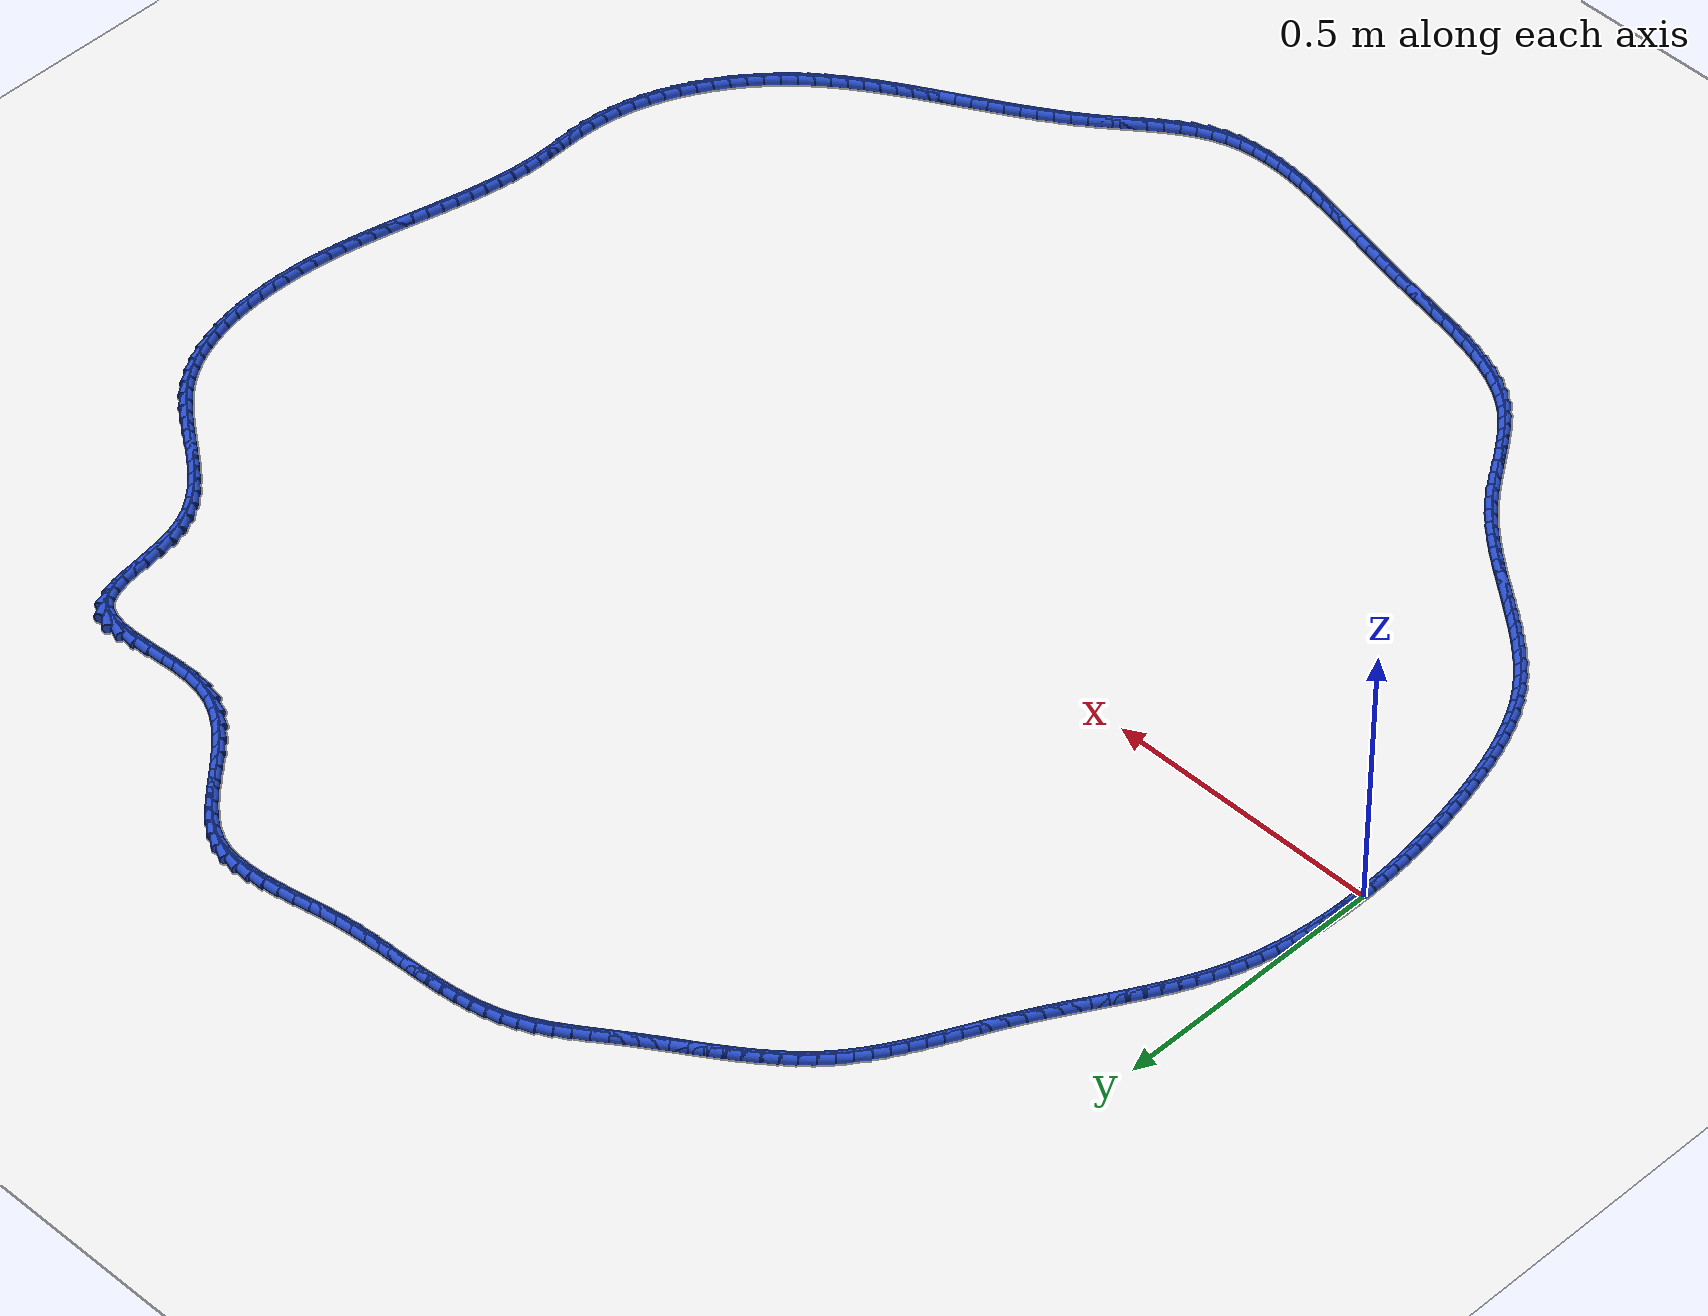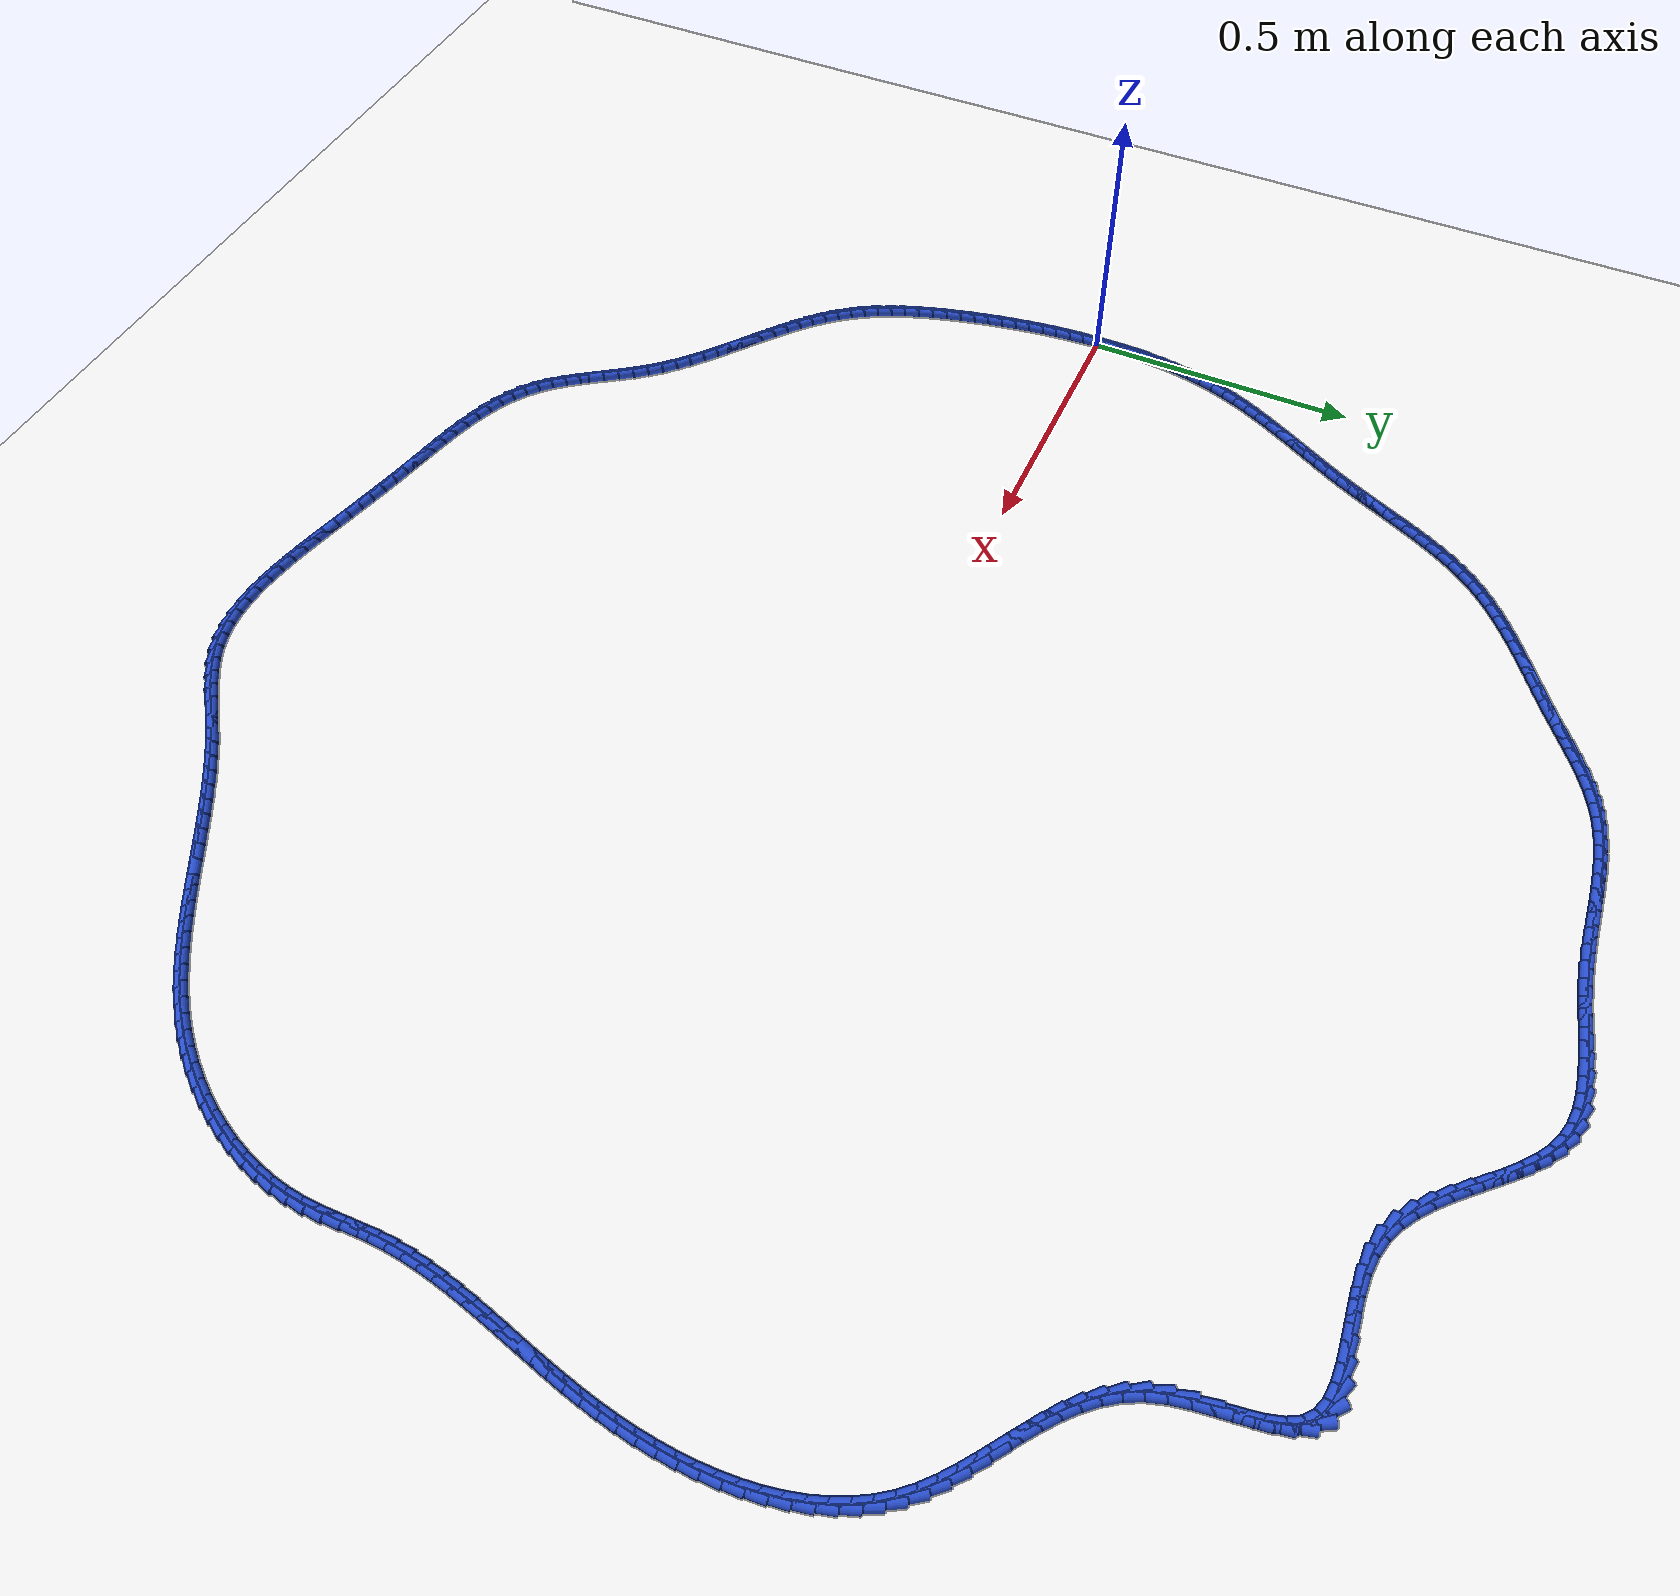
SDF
<sdf version="1.6">
 <world name="default">
  <light name="sun" type="directional">
   <pose>0 0 10 0 -0 0</pose>
   <diffuse>0.8 0.8 0.8 1</diffuse>
   <specular>0.2 0.2 0.2 1</specular>
   <attenuation>
    <range>1000</range>
    <constant>0.9</constant>
    <linear>0.01</linear>
    <quadratic>0.001</quadratic>
   </attenuation>
   <direction>-0.5 0.1 -0.9</direction>
  </light>
  <model name="ground_plane">
   <static>1</static>
   <link name="link">
    <collision name="collision">
     <geometry><plane><normal>0 0 1</normal><size>100 100</size></plane></geometry>
     <surface><friction><ode><mu>100</mu><mu2>50</mu2></ode></friction></surface>
    </collision>
    <visual name="visual">
     <cast_shadows>0</cast_shadows>
     <geometry><plane><normal>0 0 1</normal><size>100 100</size></plane></geometry>
     <material>
      <script><uri>file://media/materials/scripts/gazebo.material</uri><name>Gazebo/WhiteGlow</name></script>
     </material>
    </visual>
   </link>
  </model>
  <gravity>0 0 -9.8</gravity>
  <magnetic_field>6e-06 2.3e-05 -4.2e-05</magnetic_field>
  <atmosphere type="adiabatic"/>
  <physics name="default_physics" default="0" type="ode">
   <max_step_size>0.001</max_step_size>
   <real_time_factor>1</real_time_factor>
   <real_time_update_rate>1000</real_time_update_rate>
  </physics>
  <scene><ambient>0.4 0.4 0.4 1</ambient><background>0.7 0.7 0.7 1</background><shadows>1</shadows></scene>
  <spherical_coordinates>
   <surface_model>EARTH_WGS84</surface_model>
   <latitude_deg>0</latitude_deg>
   <longitude_deg>0</longitude_deg>
   <elevation>0</elevation>
   <heading_deg>0</heading_deg>
  </spherical_coordinates>
  <model name="line">
   <link name="link_0">
    <pose>-2.2985086056692694e-17 -8.326672684688674e-17 0.01 0 1.57 -1.5634428440553227</pose>
    <collision name="collision">
     <geometry><cylinder><radius>0.01</radius><length>0.08</length></cylinder></geometry>
    </collision>
    <visual name="visual">
     <material>
      <script><name>Gazebo/Blue</name><uri>file://media/materials/scripts/gazebo.material</uri></script>
     </material>
     <geometry><cylinder><radius>0.01</radius><length>0.08</length></cylinder></geometry>
    </visual>
   </link>
   <link name="link_1">
    <pose>-0.0002044826050421178 0.02780708496362598 0.01 0 1.57 1.5510789028608345</pose>
    <collision name="collision">
     <geometry><cylinder><radius>0.01</radius><length>0.08</length></cylinder></geometry>
    </collision>
    <visual name="visual">
     <material>
      <script><name>Gazebo/Blue</name><uri>file://media/materials/scripts/gazebo.material</uri></script>
     </material>
     <geometry><cylinder><radius>0.01</radius><length>0.08</length></cylinder></geometry>
    </visual>
   </link>
   <link name="link_2">
    <pose>0.00034536327193280674 0.055689764830520225 0.01 0 1.57 1.5217244483602832</pose>
    <collision name="collision">
     <geometry><cylinder><radius>0.01</radius><length>0.08</length></cylinder></geometry>
    </collision>
    <visual name="visual">
     <material>
      <script><name>Gazebo/Blue</name><uri>file://media/materials/scripts/gazebo.material</uri></script>
     </material>
     <geometry><cylinder><radius>0.01</radius><length>0.08</length></cylinder></geometry>
    </visual>
   </link>
   <link name="link_3">
    <pose>0.001714784121771219 0.08357378936824042 0.01 0 1.57 1.489917707448705</pose>
    <collision name="collision">
     <geometry><cylinder><radius>0.01</radius><length>0.08</length></cylinder></geometry>
    </collision>
    <visual name="visual">
     <material>
      <script><name>Gazebo/Blue</name><uri>file://media/materials/scripts/gazebo.material</uri></script>
     </material>
     <geometry><cylinder><radius>0.01</radius><length>0.08</length></cylinder></geometry>
    </visual>
   </link>
   <link name="link_4">
    <pose>0.003969026435319588 0.11138490834434424 0.01 0 1.57 1.4554804458145005</pose>
    <collision name="collision">
     <geometry><cylinder><radius>0.01</radius><length>0.08</length></cylinder></geometry>
    </collision>
    <visual name="visual">
     <material>
      <script><name>Gazebo/Blue</name><uri>file://media/materials/scripts/gazebo.material</uri></script>
     </material>
     <geometry><cylinder><radius>0.01</radius><length>0.08</length></cylinder></geometry>
    </visual>
   </link>
   <link name="link_5">
    <pose>0.007173336703424378 0.13904887152638937 0.01 0 1.57 1.4182291277863004</pose>
    <collision name="collision">
     <geometry><cylinder><radius>0.01</radius><length>0.08</length></cylinder></geometry>
    </collision>
    <visual name="visual">
     <material>
      <script><name>Gazebo/Blue</name><uri>file://media/materials/scripts/gazebo.material</uri></script>
     </material>
     <geometry><cylinder><radius>0.01</radius><length>0.08</length></cylinder></geometry>
    </visual>
   </link>
   <link name="link_6">
    <pose>0.01139296141693206 0.1664914286819335 0.01 0 1.57 1.377980974339844</pose>
    <collision name="collision">
     <geometry><cylinder><radius>0.01</radius><length>0.08</length></cylinder></geometry>
    </collision>
    <visual name="visual">
     <material>
      <script><name>Gazebo/Blue</name><uri>file://media/materials/scripts/gazebo.material</uri></script>
     </material>
     <geometry><cylinder><radius>0.01</radius><length>0.08</length></cylinder></geometry>
    </visual>
   </link>
   <link name="link_7">
    <pose>0.016693147066689104 0.19363832957853436 0.01 0 1.57 1.3345623758030936</pose>
    <collision name="collision">
     <geometry><cylinder><radius>0.01</radius><length>0.08</length></cylinder></geometry>
    </collision>
    <visual name="visual">
     <material>
      <script><name>Gazebo/Blue</name><uri>file://media/materials/scripts/gazebo.material</uri></script>
     </material>
     <geometry><cylinder><radius>0.01</radius><length>0.08</length></cylinder></geometry>
    </visual>
   </link>
   <link name="link_8">
    <pose>0.023139140143541972 0.2204153239837496 0.01 0 1.57 1.2878201085547285</pose>
    <collision name="collision">
     <geometry><cylinder><radius>0.01</radius><length>0.08</length></cylinder></geometry>
    </collision>
    <visual name="visual">
     <material>
      <script><name>Gazebo/Blue</name><uri>file://media/materials/scripts/gazebo.material</uri></script>
     </material>
     <geometry><cylinder><radius>0.01</radius><length>0.08</length></cylinder></geometry>
    </visual>
   </link>
   <link name="link_9">
    <pose>0.030796187138337143 0.246748161665137 0.01 0 1.57 1.2388443943537084</pose>
    <collision name="collision">
     <geometry><cylinder><radius>0.01</radius><length>0.08</length></cylinder></geometry>
    </collision>
    <visual name="visual">
     <material>
      <script><name>Gazebo/Blue</name><uri>file://media/materials/scripts/gazebo.material</uri></script>
     </material>
     <geometry><cylinder><radius>0.01</radius><length>0.08</length></cylinder></geometry>
    </visual>
   </link>
   <link name="link_10">
    <pose>0.03970125659712732 0.27258187699370784 0.01 0 1.57 1.1937577209074512</pose>
    <collision name="collision">
     <geometry><cylinder><radius>0.01</radius><length>0.08</length></cylinder></geometry>
    </collision>
    <visual name="visual">
     <material>
      <script><name>Gazebo/Blue</name><uri>file://media/materials/scripts/gazebo.material</uri></script>
     </material>
     <geometry><cylinder><radius>0.01</radius><length>0.08</length></cylinder></geometry>
    </visual>
   </link>
   <link name="link_11">
    <pose>0.049749779566920074 0.2979580281353544 0.01 0 1.57 1.1546983812864875</pose>
    <collision name="collision">
     <geometry><cylinder><radius>0.01</radius><length>0.08</length></cylinder></geometry>
    </collision>
    <visual name="visual">
     <material>
      <script><name>Gazebo/Blue</name><uri>file://media/materials/scripts/gazebo.material</uri></script>
     </material>
     <geometry><cylinder><radius>0.01</radius><length>0.08</length></cylinder></geometry>
    </visual>
   </link>
   <link name="link_12">
    <pose>0.06079299601231992 0.32294831008191427 0.01 0 1.57 1.1218084679741847</pose>
    <collision name="collision">
     <geometry><cylinder><radius>0.01</radius><length>0.08</length></cylinder></geometry>
    </collision>
    <visual name="visual">
     <material>
      <script><name>Gazebo/Blue</name><uri>file://media/materials/scripts/gazebo.material</uri></script>
     </material>
     <geometry><cylinder><radius>0.01</radius><length>0.08</length></cylinder></geometry>
    </visual>
   </link>
   <link name="link_13">
    <pose>0.07268213115396217 0.3476244278801135 0.01 0 1.57 1.0951256002088305</pose>
    <collision name="collision">
     <geometry><cylinder><radius>0.01</radius><length>0.08</length></cylinder></geometry>
    </collision>
    <visual name="visual">
     <material>
      <script><name>Gazebo/Blue</name><uri>file://media/materials/scripts/gazebo.material</uri></script>
     </material>
     <geometry><cylinder><radius>0.01</radius><length>0.08</length></cylinder></geometry>
    </visual>
   </link>
   <link name="link_14">
    <pose>0.08526841021248227 0.3720580865766789 0.01 0 1.57 1.074620836023597</pose>
    <collision name="collision">
     <geometry><cylinder><radius>0.01</radius><length>0.08</length></cylinder></geometry>
    </collision>
    <visual name="visual">
     <material>
      <script><name>Gazebo/Blue</name><uri>file://media/materials/scripts/gazebo.material</uri></script>
     </material>
     <geometry><cylinder><radius>0.01</radius><length>0.08</length></cylinder></geometry>
    </visual>
   </link>
   <link name="link_15">
    <pose>0.09840305840851547 0.3963209912183363 0.01 0 1.57 1.0602297704022232</pose>
    <collision name="collision">
     <geometry><cylinder><radius>0.01</radius><length>0.08</length></cylinder></geometry>
    </collision>
    <visual name="visual">
     <material>
      <script><name>Gazebo/Blue</name><uri>file://media/materials/scripts/gazebo.material</uri></script>
     </material>
     <geometry><cylinder><radius>0.01</radius><length>0.08</length></cylinder></geometry>
    </visual>
   </link>
   <link name="link_16">
    <pose>0.11193730096269733 0.42048484685181275 0.01 0 1.57 1.0518760612685927</pose>
    <collision name="collision">
     <geometry><cylinder><radius>0.01</radius><length>0.08</length></cylinder></geometry>
    </collision>
    <visual name="visual">
     <material>
      <script><name>Gazebo/Blue</name><uri>file://media/materials/scripts/gazebo.material</uri></script>
     </material>
     <geometry><cylinder><radius>0.01</radius><length>0.08</length></cylinder></geometry>
    </visual>
   </link>
   <link name="link_17">
    <pose>0.1257223630956631 0.4446213585238343 0.01 0 1.57 1.049487288630421</pose>
    <collision name="collision">
     <geometry><cylinder><radius>0.01</radius><length>0.08</length></cylinder></geometry>
    </collision>
    <visual name="visual">
     <material>
      <script><name>Gazebo/Blue</name><uri>file://media/materials/scripts/gazebo.material</uri></script>
     </material>
     <geometry><cylinder><radius>0.01</radius><length>0.08</length></cylinder></geometry>
    </visual>
   </link>
   <link name="link_18">
    <pose>0.1396094700280482 0.4688022312811273 0.01 0 1.57 1.053003639604194</pose>
    <collision name="collision">
     <geometry><cylinder><radius>0.01</radius><length>0.08</length></cylinder></geometry>
    </collision>
    <visual name="visual">
     <material>
      <script><name>Gazebo/Blue</name><uri>file://media/materials/scripts/gazebo.material</uri></script>
     </material>
     <geometry><cylinder><radius>0.01</radius><length>0.08</length></cylinder></geometry>
    </visual>
   </link>
   <link name="link_19">
    <pose>0.15344984698048791 0.4930991701704184 0.01 0 1.57 1.0623800239385943</pose>
    <collision name="collision">
     <geometry><cylinder><radius>0.01</radius><length>0.08</length></cylinder></geometry>
    </collision>
    <visual name="visual">
     <material>
      <script><name>Gazebo/Blue</name><uri>file://media/materials/scripts/gazebo.material</uri></script>
     </material>
     <geometry><cylinder><radius>0.01</radius><length>0.08</length></cylinder></geometry>
    </visual>
   </link>
   <link name="link_20">
    <pose>0.16709471917361773 0.5175838802384337 0.01 0 1.57 1.0775820916153824</pose>
    <collision name="collision">
     <geometry><cylinder><radius>0.01</radius><length>0.08</length></cylinder></geometry>
    </collision>
    <visual name="visual">
     <material>
      <script><name>Gazebo/Blue</name><uri>file://media/materials/scripts/gazebo.material</uri></script>
     </material>
     <geometry><cylinder><radius>0.01</radius><length>0.08</length></cylinder></geometry>
    </visual>
   </link>
   <link name="link_21">
    <pose>0.18039531182807303 0.5423280665319001 0.01 0 1.57 1.0977726013681997</pose>
    <collision name="collision">
     <geometry><cylinder><radius>0.01</radius><length>0.08</length></cylinder></geometry>
    </collision>
    <visual name="visual">
     <material>
      <script><name>Gazebo/Blue</name><uri>file://media/materials/scripts/gazebo.material</uri></script>
     </material>
     <geometry><cylinder><radius>0.01</radius><length>0.08</length></cylinder></geometry>
    </visual>
   </link>
   <link name="link_22">
    <pose>0.19322183296180745 0.5673908454800407 0.01 0 1.57 1.1146981909680427</pose>
    <collision name="collision">
     <geometry><cylinder><radius>0.01</radius><length>0.08</length></cylinder></geometry>
    </collision>
    <visual name="visual">
     <material>
      <script><name>Gazebo/Blue</name><uri>file://media/materials/scripts/gazebo.material</uri></script>
     </material>
     <geometry><cylinder><radius>0.01</radius><length>0.08</length></cylinder></geometry>
    </visual>
   </link>
   <link name="link_23">
    <pose>0.2056394638610435 0.5927020351870578 0.01 0 1.57 1.1235948565228195</pose>
    <collision name="collision">
     <geometry><cylinder><radius>0.01</radius><length>0.08</length></cylinder></geometry>
    </collision>
    <visual name="visual">
     <material>
      <script><name>Gazebo/Blue</name><uri>file://media/materials/scripts/gazebo.material</uri></script>
     </material>
     <geometry><cylinder><radius>0.01</radius><length>0.08</length></cylinder></geometry>
    </visual>
   </link>
   <link name="link_24">
    <pose>0.21782795713044437 0.6181154747283278 0.01 0 1.57 1.124441121660151</pose>
    <collision name="collision">
     <geometry><cylinder><radius>0.01</radius><length>0.08</length></cylinder></geometry>
    </collision>
    <visual name="visual">
     <material>
      <script><name>Gazebo/Blue</name><uri>file://media/materials/scripts/gazebo.material</uri></script>
     </material>
     <geometry><cylinder><radius>0.01</radius><length>0.08</length></cylinder></geometry>
    </visual>
   </link>
   <link name="link_25">
    <pose>0.22996852875052537 0.6434840327280049 0.01 0 1.57 1.1171889957975858</pose>
    <collision name="collision">
     <geometry><cylinder><radius>0.01</radius><length>0.08</length></cylinder></geometry>
    </collision>
    <visual name="visual">
     <material>
      <script><name>Gazebo/Blue</name><uri>file://media/materials/scripts/gazebo.material</uri></script>
     </material>
     <geometry><cylinder><radius>0.01</radius><length>0.08</length></cylinder></geometry>
    </visual>
   </link>
   <link name="link_26">
    <pose>0.24224239470180195 0.6686605778102432 0.01 0 1.57 1.1016984920163764</pose>
    <collision name="collision">
     <geometry><cylinder><radius>0.01</radius><length>0.08</length></cylinder></geometry>
    </collision>
    <visual name="visual">
     <material>
      <script><name>Gazebo/Blue</name><uri>file://media/materials/scripts/gazebo.material</uri></script>
     </material>
     <geometry><cylinder><radius>0.01</radius><length>0.08</length></cylinder></geometry>
    </visual>
   </link>
   <link name="link_27">
    <pose>0.2548307709647893 0.693497978599197 0.01 0 1.57 1.0777481087682743</pose>
    <collision name="collision">
     <geometry><cylinder><radius>0.01</radius><length>0.08</length></cylinder></geometry>
    </collision>
    <visual name="visual">
     <material>
      <script><name>Gazebo/Blue</name><uri>file://media/materials/scripts/gazebo.material</uri></script>
     </material>
     <geometry><cylinder><radius>0.01</radius><length>0.08</length></cylinder></geometry>
    </visual>
   </link>
   <link name="link_28">
    <pose>0.26791487352000276 0.7178491037190204 0.01 0 1.57 1.0450621081243905</pose>
    <collision name="collision">
     <geometry><cylinder><radius>0.01</radius><length>0.08</length></cylinder></geometry>
    </collision>
    <visual name="visual">
     <material>
      <script><name>Gazebo/Blue</name><uri>file://media/materials/scripts/gazebo.material</uri></script>
     </material>
     <geometry><cylinder><radius>0.01</radius><length>0.08</length></cylinder></geometry>
    </visual>
   </link>
   <link name="link_29">
    <pose>0.2816759183479577 0.7415668217938671 0.01 0 1.57 1.0033594229734257</pose>
    <collision name="collision">
     <geometry><cylinder><radius>0.01</radius><length>0.08</length></cylinder></geometry>
    </collision>
    <visual name="visual">
     <material>
      <script><name>Gazebo/Blue</name><uri>file://media/materials/scripts/gazebo.material</uri></script>
     </material>
     <geometry><cylinder><radius>0.01</radius><length>0.08</length></cylinder></geometry>
    </visual>
   </link>
   <link name="link_30">
    <pose>0.29629512142916936 0.7645040014478914 0.01 0 1.57 0.9524297319721574</pose>
    <collision name="collision">
     <geometry><cylinder><radius>0.01</radius><length>0.08</length></cylinder></geometry>
    </collision>
    <visual name="visual">
     <material>
      <script><name>Gazebo/Blue</name><uri>file://media/materials/scripts/gazebo.material</uri></script>
     </material>
     <geometry><cylinder><radius>0.01</radius><length>0.08</length></cylinder></geometry>
    </visual>
   </link>
   <link name="link_31">
    <pose>0.31195369874415324 0.786513511305248 0.01 0 1.57 0.8922451277999253</pose>
    <collision name="collision">
     <geometry><cylinder><radius>0.01</radius><length>0.08</length></cylinder></geometry>
    </collision>
    <visual name="visual">
     <material>
      <script><name>Gazebo/Blue</name><uri>file://media/materials/scripts/gazebo.material</uri></script>
     </material>
     <geometry><cylinder><radius>0.01</radius><length>0.08</length></cylinder></geometry>
    </visual>
   </link>
   <link name="link_32">
    <pose>0.3288327598131049 0.8074483145710609 0.01 0 1.57 0.8270134765732842</pose>
    <collision name="collision">
     <geometry><cylinder><radius>0.01</radius><length>0.08</length></cylinder></geometry>
    </collision>
    <visual name="visual">
     <material>
      <script><name>Gazebo/Blue</name><uri>file://media/materials/scripts/gazebo.material</uri></script>
     </material>
     <geometry><cylinder><radius>0.01</radius><length>0.08</length></cylinder></geometry>
    </visual>
   </link>
   <link name="link_33">
    <pose>0.34703437385355645 0.827231595060143 0.01 0 1.57 0.7681656022143313</pose>
    <collision name="collision">
     <geometry><cylinder><radius>0.01</radius><length>0.08</length></cylinder></geometry>
    </collision>
    <visual name="visual">
     <material>
      <script><name>Gazebo/Blue</name><uri>file://media/materials/scripts/gazebo.material</uri></script>
     </material>
     <geometry><cylinder><radius>0.01</radius><length>0.08</length></cylinder></geometry>
    </visual>
   </link>
   <link name="link_34">
    <pose>0.3664415420731951 0.845981159946479 0.01 0 1.57 0.7178956034454843</pose>
    <collision name="collision">
     <geometry><cylinder><radius>0.01</radius><length>0.08</length></cylinder></geometry>
    </collision>
    <visual name="visual">
     <material>
      <script><name>Gazebo/Blue</name><uri>file://media/materials/scripts/gazebo.material</uri></script>
     </material>
     <geometry><cylinder><radius>0.01</radius><length>0.08</length></cylinder></geometry>
    </visual>
   </link>
   <link name="link_35">
    <pose>0.38689962414543977 0.8638482577168629 0.01 0 1.57 0.6762352392198641</pose>
    <collision name="collision">
     <geometry><cylinder><radius>0.01</radius><length>0.08</length></cylinder></geometry>
    </collision>
    <visual name="visual">
     <material>
      <script><name>Gazebo/Blue</name><uri>file://media/materials/scripts/gazebo.material</uri></script>
     </material>
     <geometry><cylinder><radius>0.01</radius><length>0.08</length></cylinder></geometry>
    </visual>
   </link>
   <link name="link_36">
    <pose>0.40825397974370914 0.8809841368580887 0.01 0 1.57 0.6430351210413477</pose>
    <collision name="collision">
     <geometry><cylinder><radius>0.01</radius><length>0.08</length></cylinder></geometry>
    </collision>
    <visual name="visual">
     <material>
      <script><name>Gazebo/Blue</name><uri>file://media/materials/scripts/gazebo.material</uri></script>
     </material>
     <geometry><cylinder><radius>0.01</radius><length>0.08</length></cylinder></geometry>
    </visual>
   </link>
   <link name="link_37">
    <pose>0.4303499685414217 0.8975400458569507 0.01 0 1.57 0.6180583444595277</pose>
    <collision name="collision">
     <geometry><cylinder><radius>0.01</radius><length>0.08</length></cylinder></geometry>
    </collision>
    <visual name="visual">
     <material>
      <script><name>Gazebo/Blue</name><uri>file://media/materials/scripts/gazebo.material</uri></script>
     </material>
     <geometry><cylinder><radius>0.01</radius><length>0.08</length></cylinder></geometry>
    </visual>
   </link>
   <link name="link_38">
    <pose>0.45303295021199663 0.9136672332002427 0.01 0 1.57 0.6010501927074017</pose>
    <collision name="collision">
     <geometry><cylinder><radius>0.01</radius><length>0.08</length></cylinder></geometry>
    </collision>
    <visual name="visual">
     <material>
      <script><name>Gazebo/Blue</name><uri>file://media/materials/scripts/gazebo.material</uri></script>
     </material>
     <geometry><cylinder><radius>0.01</radius><length>0.08</length></cylinder></geometry>
    </visual>
   </link>
   <link name="link_39">
    <pose>0.47614828442885226 0.9295169473747587 0.01 0 1.57 0.591784837662879</pose>
    <collision name="collision">
     <geometry><cylinder><radius>0.01</radius><length>0.08</length></cylinder></geometry>
    </collision>
    <visual name="visual">
     <material>
      <script><name>Gazebo/Blue</name><uri>file://media/materials/scripts/gazebo.material</uri></script>
     </material>
     <geometry><cylinder><radius>0.01</radius><length>0.08</length></cylinder></geometry>
    </visual>
   </link>
   <link name="link_40">
    <pose>0.49954133086540764 0.9452404368672928 0.01 0 1.57 0.590092878665583</pose>
    <collision name="collision">
     <geometry><cylinder><radius>0.01</radius><length>0.08</length></cylinder></geometry>
    </collision>
    <visual name="visual">
     <material>
      <script><name>Gazebo/Blue</name><uri>file://media/materials/scripts/gazebo.material</uri></script>
     </material>
     <geometry><cylinder><radius>0.01</radius><length>0.08</length></cylinder></geometry>
    </visual>
   </link>
   <link name="link_41">
    <pose>0.5230574491950812 0.9609889501646389 0.01 0 1.57 0.5958737178467861</pose>
    <collision name="collision">
     <geometry><cylinder><radius>0.01</radius><length>0.08</length></cylinder></geometry>
    </collision>
    <visual name="visual">
     <material>
      <script><name>Gazebo/Blue</name><uri>file://media/materials/scripts/gazebo.material</uri></script>
     </material>
     <geometry><cylinder><radius>0.01</radius><length>0.08</length></cylinder></geometry>
    </visual>
   </link>
   <link name="link_42">
    <pose>0.5465419990912921 0.9769137357535914 0.01 0 1.57 0.6089687074949973</pose>
    <collision name="collision">
     <geometry><cylinder><radius>0.01</radius><length>0.08</length></cylinder></geometry>
    </collision>
    <visual name="visual">
     <material>
      <script><name>Gazebo/Blue</name><uri>file://media/materials/scripts/gazebo.material</uri></script>
     </material>
     <geometry><cylinder><radius>0.01</radius><length>0.08</length></cylinder></geometry>
    </visual>
   </link>
   <link name="link_43">
    <pose>0.5698420164162342 0.9931628160364071 0.01 0 1.57 0.6210869009097102</pose>
    <collision name="collision">
     <geometry><cylinder><radius>0.01</radius><length>0.08</length></cylinder></geometry>
    </collision>
    <visual name="visual">
     <material>
      <script><name>Gazebo/Blue</name><uri>file://media/materials/scripts/gazebo.material</uri></script>
     </material>
     <geometry><cylinder><radius>0.01</radius><length>0.08</length></cylinder></geometry>
    </visual>
   </link>
   <link name="link_44">
    <pose>0.5929145813322566 1.0096724161403416 0.01 0 1.57 0.6189211969321312</pose>
    <collision name="collision">
     <geometry><cylinder><radius>0.01</radius><length>0.08</length></cylinder></geometry>
    </collision>
    <visual name="visual">
     <material>
      <script><name>Gazebo/Blue</name><uri>file://media/materials/scripts/gazebo.material</uri></script>
     </material>
     <geometry><cylinder><radius>0.01</radius><length>0.08</length></cylinder></geometry>
    </visual>
   </link>
   <link name="link_45">
    <pose>0.6158930248125853 1.0260395392483195 0.01 0 1.57 0.6009778712239809</pose>
    <collision name="collision">
     <geometry><cylinder><radius>0.01</radius><length>0.08</length></cylinder></geometry>
    </collision>
    <visual name="visual">
     <material>
      <script><name>Gazebo/Blue</name><uri>file://media/materials/scripts/gazebo.material</uri></script>
     </material>
     <geometry><cylinder><radius>0.01</radius><length>0.08</length></cylinder></geometry>
    </visual>
   </link>
   <link name="link_46">
    <pose>0.6389265233182552 1.0418306914513293 0.01 0 1.57 0.5665466748718254</pose>
    <collision name="collision">
     <geometry><cylinder><radius>0.01</radius><length>0.08</length></cylinder></geometry>
    </collision>
    <visual name="visual">
     <material>
      <script><name>Gazebo/Blue</name><uri>file://media/materials/scripts/gazebo.material</uri></script>
     </material>
     <geometry><cylinder><radius>0.01</radius><length>0.08</length></cylinder></geometry>
    </visual>
   </link>
   <link name="link_47">
    <pose>0.6621642533103005 1.0566123788403596 0.01 0 1.57 0.5145993104859804</pose>
    <collision name="collision">
     <geometry><cylinder><radius>0.01</radius><length>0.08</length></cylinder></geometry>
    </collision>
    <visual name="visual">
     <material>
      <script><name>Gazebo/Blue</name><uri>file://media/materials/scripts/gazebo.material</uri></script>
     </material>
     <geometry><cylinder><radius>0.01</radius><length>0.08</length></cylinder></geometry>
    </visual>
   </link>
   <link name="link_48">
    <pose>0.6857553912497557 1.0699511075063983 0.01 0 1.57 0.44404951910670887</pose>
    <collision name="collision">
     <geometry><cylinder><radius>0.01</radius><length>0.08</length></cylinder></geometry>
    </collision>
    <visual name="visual">
     <material>
      <script><name>Gazebo/Blue</name><uri>file://media/materials/scripts/gazebo.material</uri></script>
     </material>
     <geometry><cylinder><radius>0.01</radius><length>0.08</length></cylinder></geometry>
    </visual>
   </link>
   <link name="link_49">
    <pose>0.7098491135976555 1.0814133835404351 0.01 0 1.57 0.35898176075363597</pose>
    <collision name="collision">
     <geometry><cylinder><radius>0.01</radius><length>0.08</length></cylinder></geometry>
    </collision>
    <visual name="visual">
     <material>
      <script><name>Gazebo/Blue</name><uri>file://media/materials/scripts/gazebo.material</uri></script>
     </material>
     <geometry><cylinder><radius>0.01</radius><length>0.08</length></cylinder></geometry>
    </visual>
   </link>
   <link name="link_50">
    <pose>0.7345631495969542 1.0906870980353853 0.01 0 1.57 0.2791735003921183</pose>
    <collision name="collision">
     <geometry><cylinder><radius>0.01</radius><length>0.08</length></cylinder></geometry>
    </collision>
    <visual name="visual">
     <material>
      <script><name>Gazebo/Blue</name><uri>file://media/materials/scripts/gazebo.material</uri></script>
     </material>
     <geometry><cylinder><radius>0.01</radius><length>0.08</length></cylinder></geometry>
    </visual>
   </link>
   <link name="link_51">
    <pose>0.7598890917260953 1.0979470249418024 0.01 0 1.57 0.2108510609055413</pose>
    <collision name="collision">
     <geometry><cylinder><radius>0.01</radius><length>0.08</length></cylinder></geometry>
    </collision>
    <visual name="visual">
     <material>
      <script><name>Gazebo/Blue</name><uri>file://media/materials/scripts/gazebo.material</uri></script>
     </material>
     <geometry><cylinder><radius>0.01</radius><length>0.08</length></cylinder></geometry>
    </visual>
   </link>
   <link name="link_52">
    <pose>0.7857869110589404 1.1034899955650825 0.01 0 1.57 0.15474594954398432</pose>
    <collision name="collision">
     <geometry><cylinder><radius>0.01</radius><length>0.08</length></cylinder></geometry>
    </collision>
    <visual name="visual">
     <material>
      <script><name>Gazebo/Blue</name><uri>file://media/materials/scripts/gazebo.material</uri></script>
     </material>
     <geometry><cylinder><radius>0.01</radius><length>0.08</length></cylinder></geometry>
    </visual>
   </link>
   <link name="link_53">
    <pose>0.8122165786693271 1.1076128412107167 0.01 0 1.57 0.11096086138013077</pose>
    <collision name="collision">
     <geometry><cylinder><radius>0.01</radius><length>0.08</length></cylinder></geometry>
    </collision>
    <visual name="visual">
     <material>
      <script><name>Gazebo/Blue</name><uri>file://media/materials/scripts/gazebo.material</uri></script>
     </material>
     <geometry><cylinder><radius>0.01</radius><length>0.08</length></cylinder></geometry>
    </visual>
   </link>
   <link name="link_54">
    <pose>0.8391380656310933 1.110612393184196 0.01 0 1.57 0.07922111700663534</pose>
    <collision name="collision">
     <geometry><cylinder><radius>0.01</radius><length>0.08</length></cylinder></geometry>
    </collision>
    <visual name="visual">
     <material>
      <script><name>Gazebo/Blue</name><uri>file://media/materials/scripts/gazebo.material</uri></script>
     </material>
     <geometry><cylinder><radius>0.01</radius><length>0.08</length></cylinder></geometry>
    </visual>
   </link>
   <link name="link_55">
    <pose>0.8665113430180766 1.1127854827910109 0.01 0 1.57 0.0590802107198235</pose>
    <collision name="collision">
     <geometry><cylinder><radius>0.01</radius><length>0.08</length></cylinder></geometry>
    </collision>
    <visual name="visual">
     <material>
      <script><name>Gazebo/Blue</name><uri>file://media/materials/scripts/gazebo.material</uri></script>
     </material>
     <geometry><cylinder><radius>0.01</radius><length>0.08</length></cylinder></geometry>
    </visual>
   </link>
   <link name="link_56">
    <pose>0.8942963819041141 1.1144289413366524 0.01 0 1.57 0.05005830667922557</pose>
    <collision name="collision">
     <geometry><cylinder><radius>0.01</radius><length>0.08</length></cylinder></geometry>
    </collision>
    <visual name="visual">
     <material>
      <script><name>Gazebo/Blue</name><uri>file://media/materials/scripts/gazebo.material</uri></script>
     </material>
     <geometry><cylinder><radius>0.01</radius><length>0.08</length></cylinder></geometry>
    </visual>
   </link>
   <link name="link_57">
    <pose>0.9224531533630438 1.1158396001266122 0.01 0 1.57 0.051718292216427625</pose>
    <collision name="collision">
     <geometry><cylinder><radius>0.01</radius><length>0.08</length></cylinder></geometry>
    </collision>
    <visual name="visual">
     <material>
      <script><name>Gazebo/Blue</name><uri>file://media/materials/scripts/gazebo.material</uri></script>
     </material>
     <geometry><cylinder><radius>0.01</radius><length>0.08</length></cylinder></geometry>
    </visual>
   </link>
   <link name="link_58">
    <pose>0.9509416284687031 1.1173142904663806 0.01 0 1.57 0.06369217819667426</pose>
    <collision name="collision">
     <geometry><cylinder><radius>0.01</radius><length>0.08</length></cylinder></geometry>
    </collision>
    <visual name="visual">
     <material>
      <script><name>Gazebo/Blue</name><uri>file://media/materials/scripts/gazebo.material</uri></script>
     </material>
     <geometry><cylinder><radius>0.01</radius><length>0.08</length></cylinder></geometry>
    </visual>
   </link>
   <link name="link_59">
    <pose>0.9797217782949296 1.1191498436614489 0.01 0 1.57 0.08566968583334234</pose>
    <collision name="collision">
     <geometry><cylinder><radius>0.01</radius><length>0.08</length></cylinder></geometry>
    </collision>
    <visual name="visual">
     <material>
      <script><name>Gazebo/Blue</name><uri>file://media/materials/scripts/gazebo.material</uri></script>
     </material>
     <geometry><cylinder><radius>0.01</radius><length>0.08</length></cylinder></geometry>
    </visual>
   </link>
   <link name="link_60">
    <pose>1.008753573915561 1.1216430910173079 0.01 0 1.57 0.11735736490985195</pose>
    <collision name="collision">
     <geometry><cylinder><radius>0.01</radius><length>0.08</length></cylinder></geometry>
    </collision>
    <visual name="visual">
     <material>
      <script><name>Gazebo/Blue</name><uri>file://media/materials/scripts/gazebo.material</uri></script>
     </material>
     <geometry><cylinder><radius>0.01</radius><length>0.08</length></cylinder></geometry>
    </visual>
   </link>
   <link name="link_61">
    <pose>1.0379969864044343 1.1250908638394481 0.01 0 1.57 0.15594105148258436</pose>
    <collision name="collision">
     <geometry><cylinder><radius>0.01</radius><length>0.08</length></cylinder></geometry>
    </collision>
    <visual name="visual">
     <material>
      <script><name>Gazebo/Blue</name><uri>file://media/materials/scripts/gazebo.material</uri></script>
     </material>
     <geometry><cylinder><radius>0.01</radius><length>0.08</length></cylinder></geometry>
    </visual>
   </link>
   <link name="link_62">
    <pose>1.0673992737470597 1.1297134181565205 0.01 0 1.57 0.18237751880735595</pose>
    <collision name="collision">
     <geometry><cylinder><radius>0.01</radius><length>0.08</length></cylinder></geometry>
    </collision>
    <visual name="visual">
     <material>
      <script><name>Gazebo/Blue</name><uri>file://media/materials/scripts/gazebo.material</uri></script>
     </material>
     <geometry><cylinder><radius>0.01</radius><length>0.08</length></cylinder></geometry>
    </visual>
   </link>
   <link name="link_63">
    <pose>1.0968091401583424 1.1351373869472416 0.01 0 1.57 0.18851819379441911</pose>
    <collision name="collision">
     <geometry><cylinder><radius>0.01</radius><length>0.08</length></cylinder></geometry>
    </collision>
    <visual name="visual">
     <material>
      <script><name>Gazebo/Blue</name><uri>file://media/materials/scripts/gazebo.material</uri></script>
     </material>
     <geometry><cylinder><radius>0.01</radius><length>0.08</length></cylinder></geometry>
    </visual>
   </link>
   <link name="link_64">
    <pose>1.1260292529229787 1.1407121070224222 0.01 0 1.57 0.1741711699503826</pose>
    <collision name="collision">
     <geometry><cylinder><radius>0.01</radius><length>0.08</length></cylinder></geometry>
    </collision>
    <visual name="visual">
     <material>
      <script><name>Gazebo/Blue</name><uri>file://media/materials/scripts/gazebo.material</uri></script>
     </material>
     <geometry><cylinder><radius>0.01</radius><length>0.08</length></cylinder></geometry>
    </visual>
   </link>
   <link name="link_65">
    <pose>1.1548620190743997 1.1457853476105395 0.01 0 1.57 0.13787477575876508</pose>
    <collision name="collision">
     <geometry><cylinder><radius>0.01</radius><length>0.08</length></cylinder></geometry>
    </collision>
    <visual name="visual">
     <material>
      <script><name>Gazebo/Blue</name><uri>file://media/materials/scripts/gazebo.material</uri></script>
     </material>
     <geometry><cylinder><radius>0.01</radius><length>0.08</length></cylinder></geometry>
    </visual>
   </link>
   <link name="link_66">
    <pose>1.1831098456460356 1.1497048779400687 0.01 0 1.57 0.07680353953465939</pose>
    <collision name="collision">
     <geometry><cylinder><radius>0.01</radius><length>0.08</length></cylinder></geometry>
    </collision>
    <visual name="visual">
     <material>
      <script><name>Gazebo/Blue</name><uri>file://media/materials/scripts/gazebo.material</uri></script>
     </material>
     <geometry><cylinder><radius>0.01</radius><length>0.08</length></cylinder></geometry>
    </visual>
   </link>
   <link name="link_67">
    <pose>1.210575139671318 1.151818467239486 0.01 0 1.57 -0.013009660916273081</pose>
    <collision name="collision">
     <geometry><cylinder><radius>0.01</radius><length>0.08</length></cylinder></geometry>
    </collision>
    <visual name="visual">
     <material>
      <script><name>Gazebo/Blue</name><uri>file://media/materials/scripts/gazebo.material</uri></script>
     </material>
     <geometry><cylinder><radius>0.01</radius><length>0.08</length></cylinder></geometry>
    </visual>
   </link>
   <link name="link_68">
    <pose>1.2370603081836768 1.1514738847372676 0.01 0 1.57 -0.13568168527107302</pose>
    <collision name="collision">
     <geometry><cylinder><radius>0.01</radius><length>0.08</length></cylinder></geometry>
    </collision>
    <visual name="visual">
     <material>
      <script><name>Gazebo/Blue</name><uri>file://media/materials/scripts/gazebo.material</uri></script>
     </material>
     <geometry><cylinder><radius>0.01</radius><length>0.08</length></cylinder></geometry>
    </visual>
   </link>
   <link name="link_69">
    <pose>1.2623677582165436 1.1480188996618892 0.01 0 1.57 -0.29291108479055494</pose>
    <collision name="collision">
     <geometry><cylinder><radius>0.01</radius><length>0.08</length></cylinder></geometry>
    </collision>
    <visual name="visual">
     <material>
      <script><name>Gazebo/Blue</name><uri>file://media/materials/scripts/gazebo.material</uri></script>
     </material>
     <geometry><cylinder><radius>0.01</radius><length>0.08</length></cylinder></geometry>
    </visual>
   </link>
   <link name="link_70">
    <pose>1.286299904714121 1.1408013024525354 0.01 0 1.57 -0.46829487335958453</pose>
    <collision name="collision">
     <geometry><cylinder><radius>0.01</radius><length>0.08</length></cylinder></geometry>
    </collision>
    <visual name="visual">
     <material>
      <script><name>Gazebo/Blue</name><uri>file://media/materials/scripts/gazebo.material</uri></script>
     </material>
     <geometry><cylinder><radius>0.01</radius><length>0.08</length></cylinder></geometry>
    </visual>
   </link>
   <link name="link_71">
    <pose>1.308760384166092 1.1294402831694286 0.01 0 1.57 -0.6127080184047947</pose>
    <collision name="collision">
     <geometry><cylinder><radius>0.01</radius><length>0.08</length></cylinder></geometry>
    </collision>
    <visual name="visual">
     <material>
      <script><name>Gazebo/Blue</name><uri>file://media/materials/scripts/gazebo.material</uri></script>
     </material>
     <geometry><cylinder><radius>0.01</radius><length>0.08</length></cylinder></geometry>
    </visual>
   </link>
   <link name="link_72">
    <pose>1.3300070526935985 1.1145047809927742 0.01 0 1.57 -0.7163576402602352</pose>
    <collision name="collision">
     <geometry><cylinder><radius>0.01</radius><length>0.08</length></cylinder></geometry>
    </collision>
    <visual name="visual">
     <material>
      <script><name>Gazebo/Blue</name><uri>file://media/materials/scripts/gazebo.material</uri></script>
     </material>
     <geometry><cylinder><radius>0.01</radius><length>0.08</length></cylinder></geometry>
    </visual>
   </link>
   <link name="link_73">
    <pose>1.3503752054053015 1.0967713678924869 0.01 0 1.57 -0.7836250346150233</pose>
    <collision name="collision">
     <geometry><cylinder><radius>0.01</radius><length>0.08</length></cylinder></geometry>
    </collision>
    <visual name="visual">
     <material>
      <script><name>Gazebo/Blue</name><uri>file://media/materials/scripts/gazebo.material</uri></script>
     </material>
     <geometry><cylinder><radius>0.01</radius><length>0.08</length></cylinder></geometry>
    </visual>
   </link>
   <link name="link_74">
    <pose>1.370200137409862 1.0770166158384782 0.01 0 1.57 -0.8194232076903748</pose>
    <collision name="collision">
     <geometry><cylinder><radius>0.01</radius><length>0.08</length></cylinder></geometry>
    </collision>
    <visual name="visual">
     <material>
      <script><name>Gazebo/Blue</name><uri>file://media/materials/scripts/gazebo.material</uri></script>
     </material>
     <geometry><cylinder><radius>0.01</radius><length>0.08</length></cylinder></geometry>
    </visual>
   </link>
   <link name="link_75">
    <pose>1.3898171438159415 1.0560170968006626 0.01 0 1.57 -0.8271901402203647</pose>
    <collision name="collision">
     <geometry><cylinder><radius>0.01</radius><length>0.08</length></cylinder></geometry>
    </collision>
    <visual name="visual">
     <material>
      <script><name>Gazebo/Blue</name><uri>file://media/materials/scripts/gazebo.material</uri></script>
     </material>
     <geometry><cylinder><radius>0.01</radius><length>0.08</length></cylinder></geometry>
    </visual>
   </link>
   <link name="link_76">
    <pose>1.409561519732201 1.0345493827489527 0.01 0 1.57 -0.8084151264426336</pose>
    <collision name="collision">
     <geometry><cylinder><radius>0.01</radius><length>0.08</length></cylinder></geometry>
    </collision>
    <visual name="visual">
     <material>
      <script><name>Gazebo/Blue</name><uri>file://media/materials/scripts/gazebo.material</uri></script>
     </material>
     <geometry><cylinder><radius>0.01</radius><length>0.08</length></cylinder></geometry>
    </visual>
   </link>
   <link name="link_77">
    <pose>1.429768560267301 1.0133900456532612 0.01 0 1.57 -0.7627480466449872</pose>
    <collision name="collision">
     <geometry><cylinder><radius>0.01</radius><length>0.08</length></cylinder></geometry>
    </collision>
    <visual name="visual">
     <material>
      <script><name>Gazebo/Blue</name><uri>file://media/materials/scripts/gazebo.material</uri></script>
     </material>
     <geometry><cylinder><radius>0.01</radius><length>0.08</length></cylinder></geometry>
    </visual>
   </link>
   <link name="link_78">
    <pose>1.450773560529904 0.9933156574835023 0.01 0 1.57 -0.6884225469282975</pose>
    <collision name="collision">
     <geometry><cylinder><radius>0.01</radius><length>0.08</length></cylinder></geometry>
    </collision>
    <visual name="visual">
     <material>
      <script><name>Gazebo/Blue</name><uri>file://media/materials/scripts/gazebo.material</uri></script>
     </material>
     <geometry><cylinder><radius>0.01</radius><length>0.08</length></cylinder></geometry>
    </visual>
   </link>
   <link name="link_79">
    <pose>1.4729118156286694 0.9751027902095885 0.01 0 1.57 -0.5832042973728933</pose>
    <collision name="collision">
     <geometry><cylinder><radius>0.01</radius><length>0.08</length></cylinder></geometry>
    </collision>
    <visual name="visual">
     <material>
      <script><name>Gazebo/Blue</name><uri>file://media/materials/scripts/gazebo.material</uri></script>
     </material>
     <geometry><cylinder><radius>0.01</radius><length>0.08</length></cylinder></geometry>
    </visual>
   </link>
   <link name="link_80">
    <pose>1.4965186206722598 0.9595280158014334 0.01 0 1.57 -0.4463358019071614</pose>
    <collision name="collision">
     <geometry><cylinder><radius>0.01</radius><length>0.08</length></cylinder></geometry>
    </collision>
    <visual name="visual">
     <material>
      <script><name>Gazebo/Blue</name><uri>file://media/materials/scripts/gazebo.material</uri></script>
     </material>
     <geometry><cylinder><radius>0.01</radius><length>0.08</length></cylinder></geometry>
    </visual>
   </link>
   <link name="link_81">
    <pose>1.5219292707693357 0.9473679062289501 0.01 0 1.57 -0.28164683155677145</pose>
    <collision name="collision">
     <geometry><cylinder><radius>0.01</radius><length>0.08</length></cylinder></geometry>
    </collision>
    <visual name="visual">
     <material>
      <script><name>Gazebo/Blue</name><uri>file://media/materials/scripts/gazebo.material</uri></script>
     </material>
     <geometry><cylinder><radius>0.01</radius><length>0.08</length></cylinder></geometry>
    </visual>
   </link>
   <link name="link_82">
    <pose>1.5494778916648841 0.9393970385069371 0.01 0 1.57 -0.11972053929166095</pose>
    <collision name="collision">
     <geometry><cylinder><radius>0.01</radius><length>0.08</length></cylinder></geometry>
    </collision>
    <visual name="visual">
     <material>
      <script><name>Gazebo/Blue</name><uri>file://media/materials/scripts/gazebo.material</uri></script>
     </material>
     <geometry><cylinder><radius>0.01</radius><length>0.08</length></cylinder></geometry>
    </visual>
   </link>
   <link name="link_83">
    <pose>1.5791677140816625 0.9358254768886025 0.01 0 1.57 -0.009647175259623046</pose>
    <collision name="collision">
     <geometry><cylinder><radius>0.01</radius><length>0.08</length></cylinder></geometry>
    </collision>
    <visual name="visual">
     <material>
      <script><name>Gazebo/Blue</name><uri>file://media/materials/scripts/gazebo.material</uri></script>
     </material>
     <geometry><cylinder><radius>0.01</radius><length>0.08</length></cylinder></geometry>
    </visual>
   </link>
   <link name="link_84">
    <pose>1.6102180576811436 0.9355259194889007 0.01 0 1.57 0.05235213067997473</pose>
    <collision name="collision">
     <geometry><cylinder><radius>0.01</radius><length>0.08</length></cylinder></geometry>
    </collision>
    <visual name="visual">
     <material>
      <script><name>Gazebo/Blue</name><uri>file://media/materials/scripts/gazebo.material</uri></script>
     </material>
     <geometry><cylinder><radius>0.01</radius><length>0.08</length></cylinder></geometry>
    </visual>
   </link>
   <link name="link_85">
    <pose>1.6417347195618885 0.9371773929221991 0.01 0 1.57 0.07325627944548552</pose>
    <collision name="collision">
     <geometry><cylinder><radius>0.01</radius><length>0.08</length></cylinder></geometry>
    </collision>
    <visual name="visual">
     <material>
      <script><name>Gazebo/Blue</name><uri>file://media/materials/scripts/gazebo.material</uri></script>
     </material>
     <geometry><cylinder><radius>0.01</radius><length>0.08</length></cylinder></geometry>
    </visual>
   </link>
   <link name="link_86">
    <pose>1.672823496822459 0.9394589238028653 0.01 0 1.57 0.053385297132067286</pose>
    <collision name="collision">
     <geometry><cylinder><radius>0.01</radius><length>0.08</length></cylinder></geometry>
    </collision>
    <visual name="visual">
     <material>
      <script><name>Gazebo/Blue</name><uri>file://media/materials/scripts/gazebo.material</uri></script>
     </material>
     <geometry><cylinder><radius>0.01</radius><length>0.08</length></cylinder></geometry>
    </visual>
   </link>
   <link name="link_87">
    <pose>1.7025901865614161 0.9410495387452662 0.01 0 1.57 -0.015289852887501414</pose>
    <collision name="collision">
     <geometry><cylinder><radius>0.01</radius><length>0.08</length></cylinder></geometry>
    </collision>
    <visual name="visual">
     <material>
      <script><name>Gazebo/Blue</name><uri>file://media/materials/scripts/gazebo.material</uri></script>
     </material>
     <geometry><cylinder><radius>0.01</radius><length>0.08</length></cylinder></geometry>
    </visual>
   </link>
   <link name="link_88">
    <pose>1.7301405858773216 0.9406282643637701 0.01 0 1.57 -0.15241555387488723</pose>
    <collision name="collision">
     <geometry><cylinder><radius>0.01</radius><length>0.08</length></cylinder></geometry>
    </collision>
    <visual name="visual">
     <material>
      <script><name>Gazebo/Blue</name><uri>file://media/materials/scripts/gazebo.material</uri></script>
     </material>
     <geometry><cylinder><radius>0.01</radius><length>0.08</length></cylinder></geometry>
    </visual>
   </link>
   <link name="link_89">
    <pose>1.7545804918687375 0.9368741272727443 0.01 0 1.57 -0.39033400247926014</pose>
    <collision name="collision">
     <geometry><cylinder><radius>0.01</radius><length>0.08</length></cylinder></geometry>
    </collision>
    <visual name="visual">
     <material>
      <script><name>Gazebo/Blue</name><uri>file://media/materials/scripts/gazebo.material</uri></script>
     </material>
     <geometry><cylinder><radius>0.01</radius><length>0.08</length></cylinder></geometry>
    </visual>
   </link>
   <link name="link_90">
    <pose>1.7750157016342243 0.9284661540865559 0.01 0 1.57 -0.7435685703942402</pose>
    <collision name="collision">
     <geometry><cylinder><radius>0.01</radius><length>0.08</length></cylinder></geometry>
    </collision>
    <visual name="visual">
     <material>
      <script><name>Gazebo/Blue</name><uri>file://media/materials/scripts/gazebo.material</uri></script>
     </material>
     <geometry><cylinder><radius>0.01</radius><length>0.08</length></cylinder></geometry>
    </visual>
   </link>
   <link name="link_91">
    <pose>1.7905960442477131 0.9141376178875782 0.01 0 1.57 -1.0767229062294053</pose>
    <collision name="collision">
     <geometry><cylinder><radius>0.01</radius><length>0.08</length></cylinder></geometry>
    </collision>
    <visual name="visual">
     <material>
      <script><name>Gazebo/Blue</name><uri>file://media/materials/scripts/gazebo.material</uri></script>
     </material>
     <geometry><cylinder><radius>0.01</radius><length>0.08</length></cylinder></geometry>
    </visual>
   </link>
   <link name="link_92">
    <pose>1.8015015380642674 0.8938909632956825 0.01 0 1.57 -1.2798442043574045</pose>
    <collision name="collision">
     <geometry><cylinder><radius>0.01</radius><length>0.08</length></cylinder></geometry>
    </collision>
    <visual name="visual">
     <material>
      <script><name>Gazebo/Blue</name><uri>file://media/materials/scripts/gazebo.material</uri></script>
     </material>
     <geometry><cylinder><radius>0.01</radius><length>0.08</length></cylinder></geometry>
    </visual>
   </link>
   <link name="link_93">
    <pose>1.80895218162309 0.869009868654917 0.01 0 1.57 -1.386170810457762</pose>
    <collision name="collision">
     <geometry><cylinder><radius>0.01</radius><length>0.08</length></cylinder></geometry>
    </collision>
    <visual name="visual">
     <material>
      <script><name>Gazebo/Blue</name><uri>file://media/materials/scripts/gazebo.material</uri></script>
     </material>
     <geometry><cylinder><radius>0.01</radius><length>0.08</length></cylinder></geometry>
    </visual>
   </link>
   <link name="link_94">
    <pose>1.8142139636742793 0.8408346712823368 0.01 0 1.57 -1.4277684400964887</pose>
    <collision name="collision">
     <geometry><cylinder><radius>0.01</radius><length>0.08</length></cylinder></geometry>
    </collision>
    <visual name="visual">
     <material>
      <script><name>Gazebo/Blue</name><uri>file://media/materials/scripts/gazebo.material</uri></script>
     </material>
     <geometry><cylinder><radius>0.01</radius><length>0.08</length></cylinder></geometry>
    </visual>
   </link>
   <link name="link_95">
    <pose>1.8185528729679334 0.8107057084949976 0.01 0 1.57 -1.4196590514495484</pose>
    <collision name="collision">
     <geometry><cylinder><radius>0.01</radius><length>0.08</length></cylinder></geometry>
    </collision>
    <visual name="visual">
     <material>
      <script><name>Gazebo/Blue</name><uri>file://media/materials/scripts/gazebo.material</uri></script>
     </material>
     <geometry><cylinder><radius>0.01</radius><length>0.08</length></cylinder></geometry>
    </visual>
   </link>
   <link name="link_96">
    <pose>1.823234898254152 0.7799633176099547 0.01 0 1.57 -1.3641909362797517</pose>
    <collision name="collision">
     <geometry><cylinder><radius>0.01</radius><length>0.08</length></cylinder></geometry>
    </collision>
    <visual name="visual">
     <material>
      <script><name>Gazebo/Blue</name><uri>file://media/materials/scripts/gazebo.material</uri></script>
     </material>
     <geometry><cylinder><radius>0.01</radius><length>0.08</length></cylinder></geometry>
    </visual>
   </link>
   <link name="link_97">
    <pose>1.8295260282830323 0.7499478359442634 0.01 0 1.57 -1.254538766493779</pose>
    <collision name="collision">
     <geometry><cylinder><radius>0.01</radius><length>0.08</length></cylinder></geometry>
    </collision>
    <visual name="visual">
     <material>
      <script><name>Gazebo/Blue</name><uri>file://media/materials/scripts/gazebo.material</uri></script>
     </material>
     <geometry><cylinder><radius>0.01</radius><length>0.08</length></cylinder></geometry>
    </visual>
   </link>
   <link name="link_98">
    <pose>1.838676787498085 0.7219844804526907 0.01 0 1.57 -1.1096673865612792</pose>
    <collision name="collision">
     <geometry><cylinder><radius>0.01</radius><length>0.08</length></cylinder></geometry>
    </collision>
    <visual name="visual">
     <material>
      <script><name>Gazebo/Blue</name><uri>file://media/materials/scripts/gazebo.material</uri></script>
     </material>
     <geometry><cylinder><radius>0.01</radius><length>0.08</length></cylinder></geometry>
    </visual>
   </link>
   <link name="link_99">
    <pose>1.8512342335210425 0.6967106471946821 0.01 0 1.57 -0.9748360166422563</pose>
    <collision name="collision">
     <geometry><cylinder><radius>0.01</radius><length>0.08</length></cylinder></geometry>
    </collision>
    <visual name="visual">
     <material>
      <script><name>Gazebo/Blue</name><uri>file://media/materials/scripts/gazebo.material</uri></script>
     </material>
     <geometry><cylinder><radius>0.01</radius><length>0.08</length></cylinder></geometry>
    </visual>
   </link>
   <link name="link_100">
    <pose>1.8667675768469254 0.6738076335689346 0.01 0 1.57 -0.8601477752397568</pose>
    <collision name="collision">
     <geometry><cylinder><radius>0.01</radius><length>0.08</length></cylinder></geometry>
    </collision>
    <visual name="visual">
     <material>
      <script><name>Gazebo/Blue</name><uri>file://media/materials/scripts/gazebo.material</uri></script>
     </material>
     <geometry><cylinder><radius>0.01</radius><length>0.08</length></cylinder></geometry>
    </visual>
   </link>
   <link name="link_101">
    <pose>1.8847738150131332 0.6528861301173221 0.01 0 1.57 -0.7689432009738546</pose>
    <collision name="collision">
     <geometry><cylinder><radius>0.01</radius><length>0.08</length></cylinder></geometry>
    </collision>
    <visual name="visual">
     <material>
      <script><name>Gazebo/Blue</name><uri>file://media/materials/scripts/gazebo.material</uri></script>
     </material>
     <geometry><cylinder><radius>0.01</radius><length>0.08</length></cylinder></geometry>
    </visual>
   </link>
   <link name="link_102">
    <pose>1.9047499455570636 0.6335568273817173 0.01 0 1.57 -0.701776170406137</pose>
    <collision name="collision">
     <geometry><cylinder><radius>0.01</radius><length>0.08</length></cylinder></geometry>
    </collision>
    <visual name="visual">
     <material>
      <script><name>Gazebo/Blue</name><uri>file://media/materials/scripts/gazebo.material</uri></script>
     </material>
     <geometry><cylinder><radius>0.01</radius><length>0.08</length></cylinder></geometry>
    </visual>
   </link>
   <link name="link_103">
    <pose>1.9261929660161152 0.6154304159039933 0.01 0 1.57 -0.6578439171109495</pose>
    <collision name="collision">
     <geometry><cylinder><radius>0.01</radius><length>0.08</length></cylinder></geometry>
    </collision>
    <visual name="visual">
     <material>
      <script><name>Gazebo/Blue</name><uri>file://media/materials/scripts/gazebo.material</uri></script>
     </material>
     <geometry><cylinder><radius>0.01</radius><length>0.08</length></cylinder></geometry>
    </visual>
   </link>
   <link name="link_104">
    <pose>1.948599873927687 0.598117586226024 0.01 0 1.57 -0.6361199803016898</pose>
    <collision name="collision">
     <geometry><cylinder><radius>0.01</radius><length>0.08</length></cylinder></geometry>
    </collision>
    <visual name="visual">
     <material>
      <script><name>Gazebo/Blue</name><uri>file://media/materials/scripts/gazebo.material</uri></script>
     </material>
     <geometry><cylinder><radius>0.01</radius><length>0.08</length></cylinder></geometry>
    </visual>
   </link>
   <link name="link_105">
    <pose>1.971467666829177 0.5812290288896823 0.01 0 1.57 -0.6360106076244355</pose>
    <collision name="collision">
     <geometry><cylinder><radius>0.01</radius><length>0.08</length></cylinder></geometry>
    </collision>
    <visual name="visual">
     <material>
      <script><name>Gazebo/Blue</name><uri>file://media/materials/scripts/gazebo.material</uri></script>
     </material>
     <geometry><cylinder><radius>0.01</radius><length>0.08</length></cylinder></geometry>
    </visual>
   </link>
   <link name="link_106">
    <pose>1.9942933422579845 0.5643754344368411 0.01 0 1.57 -0.6576398010610115</pose>
    <collision name="collision">
     <geometry><cylinder><radius>0.01</radius><length>0.08</length></cylinder></geometry>
    </collision>
    <visual name="visual">
     <material>
      <script><name>Gazebo/Blue</name><uri>file://media/materials/scripts/gazebo.material</uri></script>
     </material>
     <geometry><cylinder><radius>0.01</radius><length>0.08</length></cylinder></geometry>
    </visual>
   </link>
   <link name="link_107">
    <pose>2.016573897751508 0.5471674934093743 0.01 0 1.57 -0.7018640983453049</pose>
    <collision name="collision">
     <geometry><cylinder><radius>0.01</radius><length>0.08</length></cylinder></geometry>
    </collision>
    <visual name="visual">
     <material>
      <script><name>Gazebo/Blue</name><uri>file://media/materials/scripts/gazebo.material</uri></script>
     </material>
     <geometry><cylinder><radius>0.01</radius><length>0.08</length></cylinder></geometry>
    </visual>
   </link>
   <link name="link_108">
    <pose>2.0378063308471455 0.5292158963491549 0.01 0 1.57 -0.7700057952340165</pose>
    <collision name="collision">
     <geometry><cylinder><radius>0.01</radius><length>0.08</length></cylinder></geometry>
    </collision>
    <visual name="visual">
     <material>
      <script><name>Gazebo/Blue</name><uri>file://media/materials/scripts/gazebo.material</uri></script>
     </material>
     <geometry><cylinder><radius>0.01</radius><length>0.08</length></cylinder></geometry>
    </visual>
   </link>
   <link name="link_109">
    <pose>2.0574876390822965 0.5101313337980562 0.01 0 1.57 -0.8623699271416608</pose>
    <collision name="collision">
     <geometry><cylinder><radius>0.01</radius><length>0.08</length></cylinder></geometry>
    </collision>
    <visual name="visual">
     <material>
      <script><name>Gazebo/Blue</name><uri>file://media/materials/scripts/gazebo.material</uri></script>
     </material>
     <geometry><cylinder><radius>0.01</radius><length>0.08</length></cylinder></geometry>
    </visual>
   </link>
   <link name="link_110">
    <pose>2.075130928321309 0.4895391681696057 0.01 0 1.57 -0.9634981187758686</pose>
    <collision name="collision">
     <geometry><cylinder><radius>0.01</radius><length>0.08</length></cylinder></geometry>
    </collision>
    <visual name="visual">
     <material>
      <script><name>Gazebo/Blue</name><uri>file://media/materials/scripts/gazebo.material</uri></script>
     </material>
     <geometry><cylinder><radius>0.01</radius><length>0.08</length></cylinder></geometry>
    </visual>
   </link>
   <link name="link_111">
    <pose>2.090555009926637 0.46734320617796865 0.01 0 1.57 -1.0585389912316856</pose>
    <collision name="collision">
     <geometry><cylinder><radius>0.01</radius><length>0.08</length></cylinder></geometry>
    </collision>
    <visual name="visual">
     <material>
      <script><name>Gazebo/Blue</name><uri>file://media/materials/scripts/gazebo.material</uri></script>
     </material>
     <geometry><cylinder><radius>0.01</radius><length>0.08</length></cylinder></geometry>
    </visual>
   </link>
   <link name="link_112">
    <pose>2.103852228391037 0.44369639543153866 0.01 0 1.57 -1.1462367786478787</pose>
    <collision name="collision">
     <geometry><cylinder><radius>0.01</radius><length>0.08</length></cylinder></geometry>
    </collision>
    <visual name="visual">
     <material>
      <script><name>Gazebo/Blue</name><uri>file://media/materials/scripts/gazebo.material</uri></script>
     </material>
     <geometry><cylinder><radius>0.01</radius><length>0.08</length></cylinder></geometry>
    </visual>
   </link>
   <link name="link_113">
    <pose>2.1151245771086047 0.41876047200212396 0.01 0 1.57 -1.2263728101948455</pose>
    <collision name="collision">
     <geometry><cylinder><radius>0.01</radius><length>0.08</length></cylinder></geometry>
    </collision>
    <visual name="visual">
     <material>
      <script><name>Gazebo/Blue</name><uri>file://media/materials/scripts/gazebo.material</uri></script>
     </material>
     <geometry><cylinder><radius>0.01</radius><length>0.08</length></cylinder></geometry>
    </visual>
   </link>
   <link name="link_114">
    <pose>2.124474049473438 0.3926971719615328 0.01 0 1.57 -1.2991437690122838</pose>
    <collision name="collision">
     <geometry><cylinder><radius>0.01</radius><length>0.08</length></cylinder></geometry>
    </collision>
    <visual name="visual">
     <material>
      <script><name>Gazebo/Blue</name><uri>file://media/materials/scripts/gazebo.material</uri></script>
     </material>
     <geometry><cylinder><radius>0.01</radius><length>0.08</length></cylinder></geometry>
    </visual>
   </link>
   <link name="link_115">
    <pose>2.132002638879633 0.36566823138157317 0.01 0 1.57 -1.3650156337641595</pose>
    <collision name="collision">
     <geometry><cylinder><radius>0.01</radius><length>0.08</length></cylinder></geometry>
    </collision>
    <visual name="visual">
     <material>
      <script><name>Gazebo/Blue</name><uri>file://media/materials/scripts/gazebo.material</uri></script>
     </material>
     <geometry><cylinder><radius>0.01</radius><length>0.08</length></cylinder></geometry>
    </visual>
   </link>
   <link name="link_116">
    <pose>2.1378123387212855 0.3378353863340531 0.01 0 1.57 -1.4246018276877273</pose>
    <collision name="collision">
     <geometry><cylinder><radius>0.01</radius><length>0.08</length></cylinder></geometry>
    </collision>
    <visual name="visual">
     <material>
      <script><name>Gazebo/Blue</name><uri>file://media/materials/scripts/gazebo.material</uri></script>
     </material>
     <geometry><cylinder><radius>0.01</radius><length>0.08</length></cylinder></geometry>
    </visual>
   </link>
   <link name="link_117">
    <pose>2.142005142392493 0.30936037289078094 0.01 0 1.57 -1.478575160921656</pose>
    <collision name="collision">
     <geometry><cylinder><radius>0.01</radius><length>0.08</length></cylinder></geometry>
    </collision>
    <visual name="visual">
     <material>
      <script><name>Gazebo/Blue</name><uri>file://media/materials/scripts/gazebo.material</uri></script>
     </material>
     <geometry><cylinder><radius>0.01</radius><length>0.08</length></cylinder></geometry>
    </visual>
   </link>
   <link name="link_118">
    <pose>2.1446830432873516 0.2804049271235647 0.01 0 1.57 -1.5276112854387163</pose>
    <collision name="collision">
     <geometry><cylinder><radius>0.01</radius><length>0.08</length></cylinder></geometry>
    </collision>
    <visual name="visual">
     <material>
      <script><name>Gazebo/Blue</name><uri>file://media/materials/scripts/gazebo.material</uri></script>
     </material>
     <geometry><cylinder><radius>0.01</radius><length>0.08</length></cylinder></geometry>
    </visual>
   </link>
   <link name="link_119">
    <pose>2.145948034799957 0.2511307851042125 0.01 0 1.57 1.5692359218204361</pose>
    <collision name="collision">
     <geometry><cylinder><radius>0.01</radius><length>0.08</length></cylinder></geometry>
    </collision>
    <visual name="visual">
     <material>
      <script><name>Gazebo/Blue</name><uri>file://media/materials/scripts/gazebo.material</uri></script>
     </material>
     <geometry><cylinder><radius>0.01</radius><length>0.08</length></cylinder></geometry>
    </visual>
   </link>
   <link name="link_120">
    <pose>2.1459021103244074 0.22169968290453296 0.01 0 1.57 1.5281784598716286</pose>
    <collision name="collision">
     <geometry><cylinder><radius>0.01</radius><length>0.08</length></cylinder></geometry>
    </collision>
    <visual name="visual">
     <material>
      <script><name>Gazebo/Blue</name><uri>file://media/materials/scripts/gazebo.material</uri></script>
     </material>
     <geometry><cylinder><radius>0.01</radius><length>0.08</length></cylinder></geometry>
    </visual>
   </link>
   <link name="link_121">
    <pose>2.144647263254799 0.19227335659633318 0.01 0 1.57 1.4902535395604115</pose>
    <collision name="collision">
     <geometry><cylinder><radius>0.01</radius><length>0.08</length></cylinder></geometry>
    </collision>
    <visual name="visual">
     <material>
      <script><name>Gazebo/Blue</name><uri>file://media/materials/scripts/gazebo.material</uri></script>
     </material>
     <geometry><cylinder><radius>0.01</radius><length>0.08</length></cylinder></geometry>
    </visual>
   </link>
   <link name="link_122">
    <pose>2.1422854869852275 0.163013542251422 0.01 0 1.57 1.4549598750389396</pose>
    <collision name="collision">
     <geometry><cylinder><radius>0.01</radius><length>0.08</length></cylinder></geometry>
    </collision>
    <visual name="visual">
     <material>
      <script><name>Gazebo/Blue</name><uri>file://media/materials/scripts/gazebo.material</uri></script>
     </material>
     <geometry><cylinder><radius>0.01</radius><length>0.08</length></cylinder></geometry>
    </visual>
   </link>
   <link name="link_123">
    <pose>2.138918986624992 0.1340811164465678 0.01 0 1.57 1.422787657680819</pose>
    <collision name="collision">
     <geometry><cylinder><radius>0.01</radius><length>0.08</length></cylinder></geometry>
    </collision>
    <visual name="visual">
     <material>
      <script><name>Gazebo/Blue</name><uri>file://media/materials/scripts/gazebo.material</uri></script>
     </material>
     <geometry><cylinder><radius>0.01</radius><length>0.08</length></cylinder></geometry>
    </visual>
   </link>
   <link name="link_124">
    <pose>2.134667423963356 0.10556608730069117 0.01 0 1.57 1.3953458776986796</pose>
    <collision name="collision">
     <geometry><cylinder><radius>0.01</radius><length>0.08</length></cylinder></geometry>
    </collision>
    <visual name="visual">
     <material>
      <script><name>Gazebo/Blue</name><uri>file://media/materials/scripts/gazebo.material</uri></script>
     </material>
     <geometry><cylinder><radius>0.01</radius><length>0.08</length></cylinder></geometry>
    </visual>
   </link>
   <link name="link_125">
    <pose>2.1296806772568173 0.07743579387774244 0.01 0 1.57 1.373021577379677</pose>
    <collision name="collision">
     <geometry><cylinder><radius>0.01</radius><length>0.08</length></cylinder></geometry>
    </collision>
    <visual name="visual">
     <material>
      <script><name>Gazebo/Blue</name><uri>file://media/materials/scripts/gazebo.material</uri></script>
     </material>
     <geometry><cylinder><radius>0.01</radius><length>0.08</length></cylinder></geometry>
    </visual>
   </link>
   <link name="link_126">
    <pose>2.124111631813666 0.04964536758686199 0.01 0 1.57 1.3559997967998347</pose>
    <collision name="collision">
     <geometry><cylinder><radius>0.01</radius><length>0.08</length></cylinder></geometry>
    </collision>
    <visual name="visual">
     <material>
      <script><name>Gazebo/Blue</name><uri>file://media/materials/scripts/gazebo.material</uri></script>
     </material>
     <geometry><cylinder><radius>0.01</radius><length>0.08</length></cylinder></geometry>
    </visual>
   </link>
   <link name="link_127">
    <pose>2.1181131729421896 0.022149939837190248 0.01 0 1.57 1.3444292656731116</pose>
    <collision name="collision">
     <geometry><cylinder><radius>0.01</radius><length>0.08</length></cylinder></geometry>
    </collision>
    <visual name="visual">
     <material>
      <script><name>Gazebo/Blue</name><uri>file://media/materials/scripts/gazebo.material</uri></script>
     </material>
     <geometry><cylinder><radius>0.01</radius><length>0.08</length></cylinder></geometry>
    </visual>
   </link>
   <link name="link_128">
    <pose>2.111838185950678 -0.005095357962132296 0.01 0 1.57 1.3384351214751287</pose>
    <collision name="collision">
     <geometry><cylinder><radius>0.01</radius><length>0.08</length></cylinder></geometry>
    </collision>
    <visual name="visual">
     <material>
      <script><name>Gazebo/Blue</name><uri>file://media/materials/scripts/gazebo.material</uri></script>
     </material>
     <geometry><cylinder><radius>0.01</radius><length>0.08</length></cylinder></geometry>
    </visual>
   </link>
   <link name="link_129">
    <pose>2.105439556147421 -0.03213539440196524 0.01 0 1.57 1.3381282151093716</pose>
    <collision name="collision">
     <geometry><cylinder><radius>0.01</radius><length>0.08</length></cylinder></geometry>
    </collision>
    <visual name="visual">
     <material>
      <script><name>Gazebo/Blue</name><uri>file://media/materials/scripts/gazebo.material</uri></script>
     </material>
     <geometry><cylinder><radius>0.01</radius><length>0.08</length></cylinder></geometry>
    </visual>
   </link>
   <link name="link_130">
    <pose>2.0990701688407074 -0.05901503807316807 0.01 0 1.57 1.3436099839363422</pose>
    <collision name="collision">
     <geometry><cylinder><radius>0.01</radius><length>0.08</length></cylinder></geometry>
    </collision>
    <visual name="visual">
     <material>
      <script><name>Gazebo/Blue</name><uri>file://media/materials/scripts/gazebo.material</uri></script>
     </material>
     <geometry><cylinder><radius>0.01</radius><length>0.08</length></cylinder></geometry>
    </visual>
   </link>
   <link name="link_131">
    <pose>2.092882909338826 -0.08577915756660039 0.01 0 1.57 1.3549720751234684</pose>
    <collision name="collision">
     <geometry><cylinder><radius>0.01</radius><length>0.08</length></cylinder></geometry>
    </collision>
    <visual name="visual">
     <material>
      <script><name>Gazebo/Blue</name><uri>file://media/materials/scripts/gazebo.material</uri></script>
     </material>
     <geometry><cylinder><radius>0.01</radius><length>0.08</length></cylinder></geometry>
    </visual>
   </link>
   <link name="link_132">
    <pose>2.087030662950066 -0.11247262147312172 0.01 0 1.57 1.3722900255766097</pose>
    <collision name="collision">
     <geometry><cylinder><radius>0.01</radius><length>0.08</length></cylinder></geometry>
    </collision>
    <visual name="visual">
     <material>
      <script><name>Gazebo/Blue</name><uri>file://media/materials/scripts/gazebo.material</uri></script>
     </material>
     <geometry><cylinder><radius>0.01</radius><length>0.08</length></cylinder></geometry>
    </visual>
   </link>
   <link name="link_133">
    <pose>2.081666314982716 -0.13914029838359165 0.01 0 1.57 1.3956104615053078</pose>
    <collision name="collision">
     <geometry><cylinder><radius>0.01</radius><length>0.08</length></cylinder></geometry>
    </collision>
    <visual name="visual">
     <material>
      <script><name>Gazebo/Blue</name><uri>file://media/materials/scripts/gazebo.material</uri></script>
     </material>
     <geometry><cylinder><radius>0.01</radius><length>0.08</length></cylinder></geometry>
    </visual>
   </link>
   <link name="link_134">
    <pose>2.0769427507450664 -0.16582705688886973 0.01 0 1.57 1.4249316267299739</pose>
    <collision name="collision">
     <geometry><cylinder><radius>0.01</radius><length>0.08</length></cylinder></geometry>
    </collision>
    <visual name="visual">
     <material>
      <script><name>Gazebo/Blue</name><uri>file://media/materials/scripts/gazebo.material</uri></script>
     </material>
     <geometry><cylinder><radius>0.01</radius><length>0.08</length></cylinder></geometry>
    </visual>
   </link>
   <link name="link_135">
    <pose>2.0730128555454055 -0.19257776557981543 0.01 0 1.57 1.4601777613184292</pose>
    <collision name="collision">
     <geometry><cylinder><radius>0.01</radius><length>0.08</length></cylinder></geometry>
    </collision>
    <visual name="visual">
     <material>
      <script><name>Gazebo/Blue</name><uri>file://media/materials/scripts/gazebo.material</uri></script>
     </material>
     <geometry><cylinder><radius>0.01</radius><length>0.08</length></cylinder></geometry>
    </visual>
   </link>
   <link name="link_136">
    <pose>2.0700295146920227 -0.21943729304728843 0.01 0 1.57 1.501169076927372</pose>
    <collision name="collision">
     <geometry><cylinder><radius>0.01</radius><length>0.08</length></cylinder></geometry>
    </collision>
    <visual name="visual">
     <material>
      <script><name>Gazebo/Blue</name><uri>file://media/materials/scripts/gazebo.material</uri></script>
     </material>
     <geometry><cylinder><radius>0.01</radius><length>0.08</length></cylinder></geometry>
    </visual>
   </link>
   <link name="link_137">
    <pose>2.068145613493207 -0.2464505078821482 0.01 0 1.57 1.5475908224667234</pose>
    <collision name="collision">
     <geometry><cylinder><radius>0.01</radius><length>0.08</length></cylinder></geometry>
    </collision>
    <visual name="visual">
     <material>
      <script><name>Gazebo/Blue</name><uri>file://media/materials/scripts/gazebo.material</uri></script>
     </material>
     <geometry><cylinder><radius>0.01</radius><length>0.08</length></cylinder></geometry>
    </visual>
   </link>
   <link name="link_138">
    <pose>2.0675140372572476 -0.27366227867525433 0.01 0 1.57 -1.548735576942564</pose>
    <collision name="collision">
     <geometry><cylinder><radius>0.01</radius><length>0.08</length></cylinder></geometry>
    </collision>
    <visual name="visual">
     <material>
      <script><name>Gazebo/Blue</name><uri>file://media/materials/scripts/gazebo.material</uri></script>
     </material>
     <geometry><cylinder><radius>0.01</radius><length>0.08</length></cylinder></geometry>
    </visual>
   </link>
   <link name="link_139">
    <pose>2.068119383096862 -0.30109777556048317 0.01 0 1.57 -1.5291202352671924</pose>
    <collision name="collision">
     <geometry><cylinder><radius>0.01</radius><length>0.08</length></cylinder></geometry>
    </collision>
    <visual name="visual">
     <material>
      <script><name>Gazebo/Blue</name><uri>file://media/materials/scripts/gazebo.material</uri></script>
     </material>
     <geometry><cylinder><radius>0.01</radius><length>0.08</length></cylinder></geometry>
    </visual>
   </link>
   <link name="link_140">
    <pose>2.069270530619796 -0.32870307463805554 0.01 0 1.57 -1.5406171995265743</pose>
    <collision name="collision">
     <geometry><cylinder><radius>0.01</radius><length>0.08</length></cylinder></geometry>
    </collision>
    <visual name="visual">
     <material>
      <script><name>Gazebo/Blue</name><uri>file://media/materials/scripts/gazebo.material</uri></script>
     </material>
     <geometry><cylinder><radius>0.01</radius><length>0.08</length></cylinder></geometry>
    </visual>
   </link>
   <link name="link_141">
    <pose>2.0701067864358706 -0.3564044031626222 0.01 0 1.57 1.5585572049435437</pose>
    <collision name="collision">
     <geometry><cylinder><radius>0.01</radius><length>0.08</length></cylinder></geometry>
    </collision>
    <visual name="visual">
     <material>
      <script><name>Gazebo/Blue</name><uri>file://media/materials/scripts/gazebo.material</uri></script>
     </material>
     <geometry><cylinder><radius>0.01</radius><length>0.08</length></cylinder></geometry>
    </visual>
   </link>
   <link name="link_142">
    <pose>2.0697674571545606 -0.3841279883887933 0.01 0 1.57 1.4897760196228107</pose>
    <collision name="collision">
     <geometry><cylinder><radius>0.01</radius><length>0.08</length></cylinder></geometry>
    </collision>
    <visual name="visual">
     <material>
      <script><name>Gazebo/Blue</name><uri>file://media/materials/scripts/gazebo.material</uri></script>
     </material>
     <geometry><cylinder><radius>0.01</radius><length>0.08</length></cylinder></geometry>
    </visual>
   </link>
   <link name="link_143">
    <pose>2.0675207688086776 -0.4117972271271785 0.01 0 1.57 1.4175364703737428</pose>
    <collision name="collision">
     <geometry><cylinder><radius>0.01</radius><length>0.08</length></cylinder></geometry>
    </collision>
    <visual name="visual">
     <material>
      <script><name>Gazebo/Blue</name><uri>file://media/materials/scripts/gazebo.material</uri></script>
     </material>
     <geometry><cylinder><radius>0.01</radius><length>0.08</length></cylinder></geometry>
    </visual>
   </link>
   <link name="link_144">
    <pose>2.06326904700713 -0.43932159444335567 0.01 0 1.57 1.348758391167809</pose>
    <collision name="collision">
     <geometry><cylinder><radius>0.01</radius><length>0.08</length></cylinder></geometry>
    </collision>
    <visual name="visual">
     <material>
      <script><name>Gazebo/Blue</name><uri>file://media/materials/scripts/gazebo.material</uri></script>
     </material>
     <geometry><cylinder><radius>0.01</radius><length>0.08</length></cylinder></geometry>
    </visual>
   </link>
   <link name="link_145">
    <pose>2.057109246965025 -0.46660629228263073 0.01 0 1.57 1.2832315264192486</pose>
    <collision name="collision">
     <geometry><cylinder><radius>0.01</radius><length>0.08</length></cylinder></geometry>
    </collision>
    <visual name="visual">
     <material>
      <script><name>Gazebo/Blue</name><uri>file://media/materials/scripts/gazebo.material</uri></script>
     </material>
     <geometry><cylinder><radius>0.01</radius><length>0.08</length></cylinder></geometry>
    </visual>
   </link>
   <link name="link_146">
    <pose>2.049138375698691 -0.4935565214530081 0.01 0 1.57 1.220662281880246</pose>
    <collision name="collision">
     <geometry><cylinder><radius>0.01</radius><length>0.08</length></cylinder></geometry>
    </collision>
    <visual name="visual">
     <material>
      <script><name>Gazebo/Blue</name><uri>file://media/materials/scripts/gazebo.material</uri></script>
     </material>
     <geometry><cylinder><radius>0.01</radius><length>0.08</length></cylinder></geometry>
    </visual>
   </link>
   <link name="link_147">
    <pose>2.0394534402244555 -0.5200774827624904 0.01 0 1.57 1.1607014938859093</pose>
    <collision name="collision">
     <geometry><cylinder><radius>0.01</radius><length>0.08</length></cylinder></geometry>
    </collision>
    <visual name="visual">
     <material>
      <script><name>Gazebo/Blue</name><uri>file://media/materials/scripts/gazebo.material</uri></script>
     </material>
     <geometry><cylinder><radius>0.01</radius><length>0.08</length></cylinder></geometry>
    </visual>
   </link>
   <link name="link_148">
    <pose>2.028151447558651 -0.546074377019081 0.01 0 1.57 1.102964004471586</pose>
    <collision name="collision">
     <geometry><cylinder><radius>0.01</radius><length>0.08</length></cylinder></geometry>
    </collision>
    <visual name="visual">
     <material>
      <script><name>Gazebo/Blue</name><uri>file://media/materials/scripts/gazebo.material</uri></script>
     </material>
     <geometry><cylinder><radius>0.01</radius><length>0.08</length></cylinder></geometry>
    </visual>
   </link>
   <link name="link_149">
    <pose>2.0153294047176042 -0.571452405030783 0.01 0 1.57 1.0470421903104383</pose>
    <collision name="collision">
     <geometry><cylinder><radius>0.01</radius><length>0.08</length></cylinder></geometry>
    </collision>
    <visual name="visual">
     <material>
      <script><name>Gazebo/Blue</name><uri>file://media/materials/scripts/gazebo.material</uri></script>
     </material>
     <geometry><cylinder><radius>0.01</radius><length>0.08</length></cylinder></geometry>
    </visual>
   </link>
   <link name="link_150">
    <pose>2.0010843187176457 -0.5961167676055996 0.01 0 1.57 0.9925142822831742</pose>
    <collision name="collision">
     <geometry><cylinder><radius>0.01</radius><length>0.08</length></cylinder></geometry>
    </collision>
    <visual name="visual">
     <material>
      <script><name>Gazebo/Blue</name><uri>file://media/materials/scripts/gazebo.material</uri></script>
     </material>
     <geometry><cylinder><radius>0.01</radius><length>0.08</length></cylinder></geometry>
    </visual>
   </link>
   <link name="link_151">
    <pose>1.9855131965751047 -0.6199726655515341 0.01 0 1.57 0.9389484824659057</pose>
    <collision name="collision">
     <geometry><cylinder><radius>0.01</radius><length>0.08</length></cylinder></geometry>
    </collision>
    <visual name="visual">
     <material>
      <script><name>Gazebo/Blue</name><uri>file://media/materials/scripts/gazebo.material</uri></script>
     </material>
     <geometry><cylinder><radius>0.01</radius><length>0.08</length></cylinder></geometry>
    </visual>
   </link>
   <link name="link_152">
    <pose>1.9687130453063098 -0.6429252996765897 0.01 0 1.57 0.8859038505547642</pose>
    <collision name="collision">
     <geometry><cylinder><radius>0.01</radius><length>0.08</length></cylinder></geometry>
    </collision>
    <visual name="visual">
     <material>
      <script><name>Gazebo/Blue</name><uri>file://media/materials/scripts/gazebo.material</uri></script>
     </material>
     <geometry><cylinder><radius>0.01</radius><length>0.08</length></cylinder></geometry>
    </visual>
   </link>
   <link name="link_153">
    <pose>1.9507808719275892 -0.6648798707887694 0.01 0 1.57 0.8329288174640016</pose>
    <collision name="collision">
     <geometry><cylinder><radius>0.01</radius><length>0.08</length></cylinder></geometry>
    </collision>
    <visual name="visual">
     <material>
      <script><name>Gazebo/Blue</name><uri>file://media/materials/scripts/gazebo.material</uri></script>
     </material>
     <geometry><cylinder><radius>0.01</radius><length>0.08</length></cylinder></geometry>
    </visual>
   </link>
   <link name="link_154">
    <pose>1.931813683455275 -0.6857415796960771 0.01 0 1.57 0.7798950643243298</pose>
    <collision name="collision">
     <geometry><cylinder><radius>0.01</radius><length>0.08</length></cylinder></geometry>
    </collision>
    <visual name="visual">
     <material>
      <script><name>Gazebo/Blue</name><uri>file://media/materials/scripts/gazebo.material</uri></script>
     </material>
     <geometry><cylinder><radius>0.01</radius><length>0.08</length></cylinder></geometry>
    </visual>
   </link>
   <link name="link_155">
    <pose>1.9119086550240318 -0.7054287262663105 0.01 0 1.57 0.7298285627739514</pose>
    <collision name="collision">
     <geometry><cylinder><radius>0.01</radius><length>0.08</length></cylinder></geometry>
    </collision>
    <visual name="visual">
     <material>
      <script><name>Gazebo/Blue</name><uri>file://media/materials/scripts/gazebo.material</uri></script>
     </material>
     <geometry><cylinder><radius>0.01</radius><length>0.08</length></cylinder></geometry>
    </visual>
   </link>
   <link name="link_156">
    <pose>1.891164590951865 -0.7239865493457768 0.01 0 1.57 0.6848283657158385</pose>
    <collision name="collision">
     <geometry><cylinder><radius>0.01</radius><length>0.08</length></cylinder></geometry>
    </collision>
    <visual name="visual">
     <material>
      <script><name>Gazebo/Blue</name><uri>file://media/materials/scripts/gazebo.material</uri></script>
     </material>
     <geometry><cylinder><radius>0.01</radius><length>0.08</length></cylinder></geometry>
    </visual>
   </link>
   <link name="link_157">
    <pose>1.8696812103575895 -0.7415315651364027 0.01 0 1.57 0.6451563877351554</pose>
    <collision name="collision">
     <geometry><cylinder><radius>0.01</radius><length>0.08</length></cylinder></geometry>
    </collision>
    <visual name="visual">
     <material>
      <script><name>Gazebo/Blue</name><uri>file://media/materials/scripts/gazebo.material</uri></script>
     </material>
     <geometry><cylinder><radius>0.01</radius><length>0.08</length></cylinder></geometry>
    </visual>
   </link>
   <link name="link_158">
    <pose>1.847558242507055 -0.7581810804535143 0.01 0 1.57 0.6109434050752018</pose>
    <collision name="collision">
     <geometry><cylinder><radius>0.01</radius><length>0.08</length></cylinder></geometry>
    </collision>
    <visual name="visual">
     <material>
      <script><name>Gazebo/Blue</name><uri>file://media/materials/scripts/gazebo.material</uri></script>
     </material>
     <geometry><cylinder><radius>0.01</radius><length>0.08</length></cylinder></geometry>
    </visual>
   </link>
   <link name="link_159">
    <pose>1.8248954166661098 -0.7740524021124374 0.01 0 1.57 0.582241048737976</pose>
    <collision name="collision">
     <geometry><cylinder><radius>0.01</radius><length>0.08</length></cylinder></geometry>
    </collision>
    <visual name="visual">
     <material>
      <script><name>Gazebo/Blue</name><uri>file://media/materials/scripts/gazebo.material</uri></script>
     </material>
     <geometry><cylinder><radius>0.01</radius><length>0.08</length></cylinder></geometry>
    </visual>
   </link>
   <link name="link_160">
    <pose>1.8017924621006032 -0.7892628369284977 0.01 0 1.57 0.5590518900078861</pose>
    <collision name="collision">
     <geometry><cylinder><radius>0.01</radius><length>0.08</length></cylinder></geometry>
    </collision>
    <visual name="visual">
     <material>
      <script><name>Gazebo/Blue</name><uri>file://media/materials/scripts/gazebo.material</uri></script>
     </material>
     <geometry><cylinder><radius>0.01</radius><length>0.08</length></cylinder></geometry>
    </visual>
   </link>
   <link name="link_161">
    <pose>1.778349108076385 -0.8039296917170216 0.01 0 1.57 0.5413555399862903</pose>
    <collision name="collision">
     <geometry><cylinder><radius>0.01</radius><length>0.08</length></cylinder></geometry>
    </collision>
    <visual name="visual">
     <material>
      <script><name>Gazebo/Blue</name><uri>file://media/materials/scripts/gazebo.material</uri></script>
     </material>
     <geometry><cylinder><radius>0.01</radius><length>0.08</length></cylinder></geometry>
    </visual>
   </link>
   <link name="link_162">
    <pose>1.754665083859303 -0.8181702732933342 0.01 0 1.57 0.5291297534630568</pose>
    <collision name="collision">
     <geometry><cylinder><radius>0.01</radius><length>0.08</length></cylinder></geometry>
    </collision>
    <visual name="visual">
     <material>
      <script><name>Gazebo/Blue</name><uri>file://media/materials/scripts/gazebo.material</uri></script>
     </material>
     <geometry><cylinder><radius>0.01</radius><length>0.08</length></cylinder></geometry>
    </visual>
   </link>
   <link name="link_163">
    <pose>1.7308401187152076 -0.8321018884727626 0.01 0 1.57 0.5220765039864893</pose>
    <collision name="collision">
     <geometry><cylinder><radius>0.01</radius><length>0.08</length></cylinder></geometry>
    </collision>
    <visual name="visual">
     <material>
      <script><name>Gazebo/Blue</name><uri>file://media/materials/scripts/gazebo.material</uri></script>
     </material>
     <geometry><cylinder><radius>0.01</radius><length>0.08</length></cylinder></geometry>
    </visual>
   </link>
   <link name="link_164">
    <pose>1.7069632140130602 -0.8458388055028 0.01 0 1.57 0.519037538598423</pose>
    <collision name="collision">
     <geometry><cylinder><radius>0.01</radius><length>0.08</length></cylinder></geometry>
    </collision>
    <visual name="visual">
     <material>
      <script><name>Gazebo/Blue</name><uri>file://media/materials/scripts/gazebo.material</uri></script>
     </material>
     <geometry><cylinder><radius>0.01</radius><length>0.08</length></cylinder></geometry>
    </visual>
   </link>
   <link name="link_165">
    <pose>1.6830798929299817 -0.8594829778747042 0.01 0 1.57 0.5197369578744229</pose>
    <collision name="collision">
     <geometry><cylinder><radius>0.01</radius><length>0.08</length></cylinder></geometry>
    </collision>
    <visual name="visual">
     <material>
      <script><name>Gazebo/Blue</name><uri>file://media/materials/scripts/gazebo.material</uri></script>
     </material>
     <geometry><cylinder><radius>0.01</radius><length>0.08</length></cylinder></geometry>
    </visual>
   </link>
   <link name="link_166">
    <pose>1.6592246655787115 -0.8731332397411036 0.01 0 1.57 0.524181992881121</pose>
    <collision name="collision">
     <geometry><cylinder><radius>0.01</radius><length>0.08</length></cylinder></geometry>
    </collision>
    <visual name="visual">
     <material>
      <script><name>Gazebo/Blue</name><uri>file://media/materials/scripts/gazebo.material</uri></script>
     </material>
     <geometry><cylinder><radius>0.01</radius><length>0.08</length></cylinder></geometry>
    </visual>
   </link>
   <link name="link_167">
    <pose>1.6354320420710828 -0.8868884252543711 0.01 0 1.57 0.5323636918302034</pose>
    <collision name="collision">
     <geometry><cylinder><radius>0.01</radius><length>0.08</length></cylinder></geometry>
    </collision>
    <visual name="visual">
     <material>
      <script><name>Gazebo/Blue</name><uri>file://media/materials/scripts/gazebo.material</uri></script>
     </material>
     <geometry><cylinder><radius>0.01</radius><length>0.08</length></cylinder></geometry>
    </visual>
   </link>
   <link name="link_168">
    <pose>1.6117365325189263 -0.9008473685668779 0.01 0 1.57 0.5442551252715483</pose>
    <collision name="collision">
     <geometry><cylinder><radius>0.01</radius><length>0.08</length></cylinder></geometry>
    </collision>
    <visual name="visual">
     <material>
      <script><name>Gazebo/Blue</name><uri>file://media/materials/scripts/gazebo.material</uri></script>
     </material>
     <geometry><cylinder><radius>0.01</radius><length>0.08</length></cylinder></geometry>
    </visual>
   </link>
   <link name="link_169">
    <pose>1.588172647034073 -0.9151089038309959 0.01 0 1.57 0.559808290816162</pose>
    <collision name="collision">
     <geometry><cylinder><radius>0.01</radius><length>0.08</length></cylinder></geometry>
    </collision>
    <visual name="visual">
     <material>
      <script><name>Gazebo/Blue</name><uri>file://media/materials/scripts/gazebo.material</uri></script>
     </material>
     <geometry><cylinder><radius>0.01</radius><length>0.08</length></cylinder></geometry>
    </visual>
   </link>
   <link name="link_170">
    <pose>1.5647748957283558 -0.9297718651990975 0.01 0 1.57 0.5789499145410457</pose>
    <collision name="collision">
     <geometry><cylinder><radius>0.01</radius><length>0.08</length></cylinder></geometry>
    </collision>
    <visual name="visual">
     <material>
      <script><name>Gazebo/Blue</name><uri>file://media/materials/scripts/gazebo.material</uri></script>
     </material>
     <geometry><cylinder><radius>0.01</radius><length>0.08</length></cylinder></geometry>
    </visual>
   </link>
   <link name="link_171">
    <pose>1.541577788713605 -0.9449350868235543 0.01 0 1.57 0.6015764757833516</pose>
    <collision name="collision">
     <geometry><cylinder><radius>0.01</radius><length>0.08</length></cylinder></geometry>
    </collision>
    <visual name="visual">
     <material>
      <script><name>Gazebo/Blue</name><uri>file://media/materials/scripts/gazebo.material</uri></script>
     </material>
     <geometry><cylinder><radius>0.01</radius><length>0.08</length></cylinder></geometry>
    </visual>
   </link>
   <link name="link_172">
    <pose>1.5186158361016528 -0.9606974028567381 0.01 0 1.57 0.6275489284822567</pose>
    <collision name="collision">
     <geometry><cylinder><radius>0.01</radius><length>0.08</length></cylinder></geometry>
    </collision>
    <visual name="visual">
     <material>
      <script><name>Gazebo/Blue</name><uri>file://media/materials/scripts/gazebo.material</uri></script>
     </material>
     <geometry><cylinder><radius>0.01</radius><length>0.08</length></cylinder></geometry>
    </visual>
   </link>
   <link name="link_173">
    <pose>1.4959235480043307 -0.9771576474510211 0.01 0 1.57 0.6554982507071997</pose>
    <collision name="collision">
     <geometry><cylinder><radius>0.01</radius><length>0.08</length></cylinder></geometry>
    </collision>
    <visual name="visual">
     <material>
      <script><name>Gazebo/Blue</name><uri>file://media/materials/scripts/gazebo.material</uri></script>
     </material>
     <geometry><cylinder><radius>0.01</radius><length>0.08</length></cylinder></geometry>
    </visual>
   </link>
   <link name="link_174">
    <pose>1.4735238959219301 -0.9943811129166319 0.01 0 1.57 0.6723886418195917</pose>
    <collision name="collision">
     <geometry><cylinder><radius>0.01</radius><length>0.08</length></cylinder></geometry>
    </collision>
    <visual name="visual">
     <material>
      <script><name>Gazebo/Blue</name><uri>file://media/materials/scripts/gazebo.material</uri></script>
     </material>
     <geometry><cylinder><radius>0.01</radius><length>0.08</length></cylinder></geometry>
    </visual>
   </link>
   <link name="link_175">
    <pose>1.4513129895394947 -1.0120643141796015 0.01 0 1.57 0.6705403723813222</pose>
    <collision name="collision">
     <geometry><cylinder><radius>0.01</radius><length>0.08</length></cylinder></geometry>
    </collision>
    <visual name="visual">
     <material>
      <script><name>Gazebo/Blue</name><uri>file://media/materials/scripts/gazebo.material</uri></script>
     </material>
     <geometry><cylinder><radius>0.01</radius><length>0.08</length></cylinder></geometry>
    </visual>
   </link>
   <link name="link_176">
    <pose>1.429108419055501 -1.0296755161538667 0.01 0 1.57 0.6496976289407056</pose>
    <collision name="collision">
     <geometry><cylinder><radius>0.01</radius><length>0.08</length></cylinder></geometry>
    </collision>
    <visual name="visual">
     <material>
      <script><name>Gazebo/Blue</name><uri>file://media/materials/scripts/gazebo.material</uri></script>
     </material>
     <geometry><cylinder><radius>0.01</radius><length>0.08</length></cylinder></geometry>
    </visual>
   </link>
   <link name="link_177">
    <pose>1.4067266076742866 -1.046679591392594 0.01 0 1.57 0.6090117469464895</pose>
    <collision name="collision">
     <geometry><cylinder><radius>0.01</radius><length>0.08</length></cylinder></geometry>
    </collision>
    <visual name="visual">
     <material>
      <script><name>Gazebo/Blue</name><uri>file://media/materials/scripts/gazebo.material</uri></script>
     </material>
     <geometry><cylinder><radius>0.01</radius><length>0.08</length></cylinder></geometry>
    </visual>
   </link>
   <link name="link_178">
    <pose>1.3839839786001917 -1.0625414124489478 0.01 0 1.57 0.5470936378254092</pose>
    <collision name="collision">
     <geometry><cylinder><radius>0.01</radius><length>0.08</length></cylinder></geometry>
    </collision>
    <visual name="visual">
     <material>
      <script><name>Gazebo/Blue</name><uri>file://media/materials/scripts/gazebo.material</uri></script>
     </material>
     <geometry><cylinder><radius>0.01</radius><length>0.08</length></cylinder></geometry>
    </visual>
   </link>
   <link name="link_179">
    <pose>1.3606969550375538 -1.0767258518760934 0.01 0 1.57 0.46246207841684284</pose>
    <collision name="collision">
     <geometry><cylinder><radius>0.01</radius><length>0.08</length></cylinder></geometry>
    </collision>
    <visual name="visual">
     <material>
      <script><name>Gazebo/Blue</name><uri>file://media/materials/scripts/gazebo.material</uri></script>
     </material>
     <geometry><cylinder><radius>0.01</radius><length>0.08</length></cylinder></geometry>
    </visual>
   </link>
   <link name="link_180">
    <pose>1.3366819601907127 -1.0886977822271962 0.01 0 1.57 0.35498244303026244</pose>
    <collision name="collision">
     <geometry><cylinder><radius>0.01</radius><length>0.08</length></cylinder></geometry>
    </collision>
    <visual name="visual">
     <material>
      <script><name>Gazebo/Blue</name><uri>file://media/materials/scripts/gazebo.material</uri></script>
     </material>
     <geometry><cylinder><radius>0.01</radius><length>0.08</length></cylinder></geometry>
    </visual>
   </link>
   <link name="link_181">
    <pose>1.311760809189643 -1.0979356831296947 0.01 0 1.57 0.24119229416348173</pose>
    <collision name="collision">
     <geometry><cylinder><radius>0.01</radius><length>0.08</length></cylinder></geometry>
    </collision>
    <visual name="visual">
     <material>
      <script><name>Gazebo/Blue</name><uri>file://media/materials/scripts/gazebo.material</uri></script>
     </material>
     <geometry><cylinder><radius>0.01</radius><length>0.08</length></cylinder></geometry>
    </visual>
   </link>
   <link name="link_182">
    <pose>1.2859049786347023 -1.1042957201957333 0.01 0 1.57 0.13999442233161233</pose>
    <collision name="collision">
     <geometry><cylinder><radius>0.01</radius><length>0.08</length></cylinder></geometry>
    </collision>
    <visual name="visual">
     <material>
      <script><name>Gazebo/Blue</name><uri>file://media/materials/scripts/gazebo.material</uri></script>
     </material>
     <geometry><cylinder><radius>0.01</radius><length>0.08</length></cylinder></geometry>
    </visual>
   </link>
   <link name="link_183">
    <pose>1.259251415050391 -1.1080516392675508 0.01 0 1.57 0.052948682502865815</pose>
    <collision name="collision">
     <geometry><cylinder><radius>0.01</radius><length>0.08</length></cylinder></geometry>
    </collision>
    <visual name="visual">
     <material>
      <script><name>Gazebo/Blue</name><uri>file://media/materials/scripts/gazebo.material</uri></script>
     </material>
     <geometry><cylinder><radius>0.01</radius><length>0.08</length></cylinder></geometry>
    </visual>
   </link>
   <link name="link_184">
    <pose>1.2319456285743622 -1.1094987973385952 0.01 0 1.57 -0.020356592686012392</pose>
    <collision name="collision">
     <geometry><cylinder><radius>0.01</radius><length>0.08</length></cylinder></geometry>
    </collision>
    <visual name="visual">
     <material>
      <script><name>Gazebo/Blue</name><uri>file://media/materials/scripts/gazebo.material</uri></script>
     </material>
     <geometry><cylinder><radius>0.01</radius><length>0.08</length></cylinder></geometry>
    </visual>
   </link>
   <link name="link_185">
    <pose>1.2041331293442687 -1.1089325514023127 0.01 0 1.57 -0.080901939213322</pose>
    <collision name="collision">
     <geometry><cylinder><radius>0.01</radius><length>0.08</length></cylinder></geometry>
    </collision>
    <visual name="visual">
     <material>
      <script><name>Gazebo/Blue</name><uri>file://media/materials/scripts/gazebo.material</uri></script>
     </material>
     <geometry><cylinder><radius>0.01</radius><length>0.08</length></cylinder></geometry>
    </visual>
   </link>
   <link name="link_186">
    <pose>1.1759594274977645 -1.1066482584521506 0.01 0 1.57 -0.12984171581247755</pose>
    <collision name="collision">
     <geometry><cylinder><radius>0.01</radius><length>0.08</length></cylinder></geometry>
    </collision>
    <visual name="visual">
     <material>
      <script><name>Gazebo/Blue</name><uri>file://media/materials/scripts/gazebo.material</uri></script>
     </material>
     <geometry><cylinder><radius>0.01</radius><length>0.08</length></cylinder></geometry>
    </visual>
   </link>
   <link name="link_187">
    <pose>1.147570033172503 -1.1029412754815568 0.01 0 1.57 -0.16825997094299877</pose>
    <collision name="collision">
     <geometry><cylinder><radius>0.01</radius><length>0.08</length></cylinder></geometry>
    </collision>
    <visual name="visual">
     <material>
      <script><name>Gazebo/Blue</name><uri>file://media/materials/scripts/gazebo.material</uri></script>
     </material>
     <geometry><cylinder><radius>0.01</radius><length>0.08</length></cylinder></geometry>
    </visual>
   </link>
   <link name="link_188">
    <pose>1.119110456506137 -1.0981069594839776 0.01 0 1.57 -0.19703788254680052</pose>
    <collision name="collision">
     <geometry><cylinder><radius>0.01</radius><length>0.08</length></cylinder></geometry>
    </collision>
    <visual name="visual">
     <material>
      <script><name>Gazebo/Blue</name><uri>file://media/materials/scripts/gazebo.material</uri></script>
     </material>
     <geometry><cylinder><radius>0.01</radius><length>0.08</length></cylinder></geometry>
    </visual>
   </link>
   <link name="link_189">
    <pose>1.09072620763632 -1.0924406674528606 0.01 0 1.57 -0.21678603557533555</pose>
    <collision name="collision">
     <geometry><cylinder><radius>0.01</radius><length>0.08</length></cylinder></geometry>
    </collision>
    <visual name="visual">
     <material>
      <script><name>Gazebo/Blue</name><uri>file://media/materials/scripts/gazebo.material</uri></script>
     </material>
     <geometry><cylinder><radius>0.01</radius><length>0.08</length></cylinder></geometry>
    </visual>
   </link>
   <link name="link_190">
    <pose>1.0625627967007052 -1.086237756381652 0.01 0 1.57 -0.227805066888016</pose>
    <collision name="collision">
     <geometry><cylinder><radius>0.01</radius><length>0.08</length></cylinder></geometry>
    </collision>
    <visual name="visual">
     <material>
      <script><name>Gazebo/Blue</name><uri>file://media/materials/scripts/gazebo.material</uri></script>
     </material>
     <geometry><cylinder><radius>0.01</radius><length>0.08</length></cylinder></geometry>
    </visual>
   </link>
   <link name="link_191">
    <pose>1.0347657338369465 -1.0797935832638004 0.01 0 1.57 -0.2310871649107776</pose>
    <collision name="collision">
     <geometry><cylinder><radius>0.01</radius><length>0.08</length></cylinder></geometry>
    </collision>
    <visual name="visual">
     <material>
      <script><name>Gazebo/Blue</name><uri>file://media/materials/scripts/gazebo.material</uri></script>
     </material>
     <geometry><cylinder><radius>0.01</radius><length>0.08</length></cylinder></geometry>
    </visual>
   </link>
   <link name="link_192">
    <pose>1.007438056918966 -1.073363642644059 0.01 0 1.57 -0.2311968925453582</pose>
    <collision name="collision">
     <geometry><cylinder><radius>0.01</radius><length>0.08</length></cylinder></geometry>
    </collision>
    <visual name="visual">
     <material>
      <script><name>Gazebo/Blue</name><uri>file://media/materials/scripts/gazebo.material</uri></script>
     </material>
     <geometry><cylinder><radius>0.01</radius><length>0.08</length></cylinder></geometry>
    </visual>
   </link>
   <link name="link_193">
    <pose>0.9804863445492367 -1.0670190417296463 0.01 0 1.57 -0.22942280729182085</pose>
    <collision name="collision">
     <geometry><cylinder><radius>0.01</radius><length>0.08</length></cylinder></geometry>
    </collision>
    <visual name="visual">
     <material>
      <script><name>Gazebo/Blue</name><uri>file://media/materials/scripts/gazebo.material</uri></script>
     </material>
     <geometry><cylinder><radius>0.01</radius><length>0.08</length></cylinder></geometry>
    </visual>
   </link>
   <link name="link_194">
    <pose>0.9537604108312575 -1.060777611266176 0.01 0 1.57 -0.2257424493339475</pose>
    <collision name="collision">
     <geometry><cylinder><radius>0.01</radius><length>0.08</length></cylinder></geometry>
    </collision>
    <visual name="visual">
     <material>
      <script><name>Gazebo/Blue</name><uri>file://media/materials/scripts/gazebo.material</uri></script>
     </material>
     <geometry><cylinder><radius>0.01</radius><length>0.08</length></cylinder></geometry>
    </visual>
   </link>
   <link name="link_195">
    <pose>0.9271100642907885 -1.0546571767642607 0.01 0 1.57 -0.22019224846852214</pose>
    <collision name="collision">
     <geometry><cylinder><radius>0.01</radius><length>0.08</length></cylinder></geometry>
    </collision>
    <visual name="visual">
     <material>
      <script><name>Gazebo/Blue</name><uri>file://media/materials/scripts/gazebo.material</uri></script>
     </material>
     <geometry><cylinder><radius>0.01</radius><length>0.08</length></cylinder></geometry>
    </visual>
   </link>
   <link name="link_196">
    <pose>0.9003851134535875 -1.0486755637345113 0.01 0 1.57 -0.21286723119529138</pose>
    <collision name="collision">
     <geometry><cylinder><radius>0.01</radius><length>0.08</length></cylinder></geometry>
    </collision>
    <visual name="visual">
     <material>
      <script><name>Gazebo/Blue</name><uri>file://media/materials/scripts/gazebo.material</uri></script>
     </material>
     <geometry><cylinder><radius>0.01</radius><length>0.08</length></cylinder></geometry>
    </visual>
   </link>
   <link name="link_197">
    <pose>0.873435366845414 -1.04285059768754 0.01 0 1.57 -0.20391622572733256</pose>
    <collision name="collision">
     <geometry><cylinder><radius>0.01</radius><length>0.08</length></cylinder></geometry>
    </collision>
    <visual name="visual">
     <material>
      <script><name>Gazebo/Blue</name><uri>file://media/materials/scripts/gazebo.material</uri></script>
     </material>
     <geometry><cylinder><radius>0.01</radius><length>0.08</length></cylinder></geometry>
    </visual>
   </link>
   <link name="link_198">
    <pose>0.8461106333311484 -1.0372001039010736 0.01 0 1.57 -0.19555950271715009</pose>
    <collision name="collision">
     <geometry><cylinder><radius>0.01</radius><length>0.08</length></cylinder></geometry>
    </collision>
    <visual name="visual">
     <material>
      <script><name>Gazebo/Blue</name><uri>file://media/materials/scripts/gazebo.material</uri></script>
     </material>
     <geometry><cylinder><radius>0.01</radius><length>0.08</length></cylinder></geometry>
    </visual>
   </link>
   <link name="link_199">
    <pose>0.8183269795819313 -1.0316964066069982 0.01 0 1.57 -0.19541677949048863</pose>
    <collision name="collision">
     <geometry><cylinder><radius>0.01</radius><length>0.08</length></cylinder></geometry>
    </collision>
    <visual name="visual">
     <material>
      <script><name>Gazebo/Blue</name><uri>file://media/materials/scripts/gazebo.material</uri></script>
     </material>
     <geometry><cylinder><radius>0.01</radius><length>0.08</length></cylinder></geometry>
    </visual>
   </link>
   <link name="link_200">
    <pose>0.7902519262725237 -1.0261391497027368 0.01 0 1.57 -0.2050472013083898</pose>
    <collision name="collision">
     <geometry><cylinder><radius>0.01</radius><length>0.08</length></cylinder></geometry>
    </collision>
    <visual name="visual">
     <material>
      <script><name>Gazebo/Blue</name><uri>file://media/materials/scripts/gazebo.material</uri></script>
     </material>
     <geometry><cylinder><radius>0.01</radius><length>0.08</length></cylinder></geometry>
    </visual>
   </link>
   <link name="link_201">
    <pose>0.7621126354598751 -1.020287019719054 0.01 0 1.57 -0.22449777829286993</pose>
    <collision name="collision">
     <geometry><cylinder><radius>0.01</radius><length>0.08</length></cylinder></geometry>
    </collision>
    <visual name="visual">
     <material>
      <script><name>Gazebo/Blue</name><uri>file://media/materials/scripts/gazebo.material</uri></script>
     </material>
     <geometry><cylinder><radius>0.01</radius><length>0.08</length></cylinder></geometry>
    </visual>
   </link>
   <link name="link_202">
    <pose>0.734136269200935 -1.0138987031867126 0.01 0 1.57 -0.2541433965901949</pose>
    <collision name="collision">
     <geometry><cylinder><radius>0.01</radius><length>0.08</length></cylinder></geometry>
    </collision>
    <visual name="visual">
     <material>
      <script><name>Gazebo/Blue</name><uri>file://media/materials/scripts/gazebo.material</uri></script>
     </material>
     <geometry><cylinder><radius>0.01</radius><length>0.08</length></cylinder></geometry>
    </visual>
   </link>
   <link name="link_203">
    <pose>0.7065499895526535 -1.0067328866364778 0.01 0 1.57 -0.2946487154816712</pose>
    <collision name="collision">
     <geometry><cylinder><radius>0.01</radius><length>0.08</length></cylinder></geometry>
    </collision>
    <visual name="visual">
     <material>
      <script><name>Gazebo/Blue</name><uri>file://media/materials/scripts/gazebo.material</uri></script>
     </material>
     <geometry><cylinder><radius>0.01</radius><length>0.08</length></cylinder></geometry>
    </visual>
   </link>
   <link name="link_204">
    <pose>0.6795809585719799 -0.9985482565991125 0.01 0 1.57 -0.34690677578327367</pose>
    <collision name="collision">
     <geometry><cylinder><radius>0.01</radius><length>0.08</length></cylinder></geometry>
    </collision>
    <visual name="visual">
     <material>
      <script><name>Gazebo/Blue</name><uri>file://media/materials/scripts/gazebo.material</uri></script>
     </material>
     <geometry><cylinder><radius>0.01</radius><length>0.08</length></cylinder></geometry>
    </visual>
   </link>
   <link name="link_205">
    <pose>0.653456338315864 -0.989103499605381 0.01 0 1.57 -0.41192418580479384</pose>
    <collision name="collision">
     <geometry><cylinder><radius>0.01</radius><length>0.08</length></cylinder></geometry>
    </collision>
    <visual name="visual">
     <material>
      <script><name>Gazebo/Blue</name><uri>file://media/materials/scripts/gazebo.material</uri></script>
     </material>
     <geometry><cylinder><radius>0.01</radius><length>0.08</length></cylinder></geometry>
    </visual>
   </link>
   <link name="link_206">
    <pose>0.6284032908412552 -0.9781573021860471 0.01 0 1.57 -0.49061209112960336</pose>
    <collision name="collision">
     <geometry><cylinder><radius>0.01</radius><length>0.08</length></cylinder></geometry>
    </collision>
    <visual name="visual">
     <material>
      <script><name>Gazebo/Blue</name><uri>file://media/materials/scripts/gazebo.material</uri></script>
     </material>
     <geometry><cylinder><radius>0.01</radius><length>0.08</length></cylinder></geometry>
    </visual>
   </link>
   <link name="link_207">
    <pose>0.6046489782051035 -0.9654683508718751 0.01 0 1.57 -0.5834439598080575</pose>
    <collision name="collision">
     <geometry><cylinder><radius>0.01</radius><length>0.08</length></cylinder></geometry>
    </collision>
    <visual name="visual">
     <material>
      <script><name>Gazebo/Blue</name><uri>file://media/materials/scripts/gazebo.material</uri></script>
     </material>
     <geometry><cylinder><radius>0.01</radius><length>0.08</length></cylinder></geometry>
    </visual>
   </link>
   <link name="link_208">
    <pose>0.5824205624643586 -0.9507953321936287 0.01 0 1.57 -0.6892367860913915</pose>
    <collision name="collision">
     <geometry><cylinder><radius>0.01</radius><length>0.08</length></cylinder></geometry>
    </collision>
    <visual name="visual">
     <material>
      <script><name>Gazebo/Blue</name><uri>file://media/materials/scripts/gazebo.material</uri></script>
     </material>
     <geometry><cylinder><radius>0.01</radius><length>0.08</length></cylinder></geometry>
    </visual>
   </link>
   <link name="link_209">
    <pose>0.5619319736198143 -0.9339116324327507 0.01 0 1.57 -0.7900097394956082</pose>
    <collision name="collision">
     <geometry><cylinder><radius>0.01</radius><length>0.08</length></cylinder></geometry>
    </collision>
    <visual name="visual">
     <material>
      <script><name>Gazebo/Blue</name><uri>file://media/materials/scripts/gazebo.material</uri></script>
     </material>
     <geometry><cylinder><radius>0.01</radius><length>0.08</length></cylinder></geometry>
    </visual>
   </link>
   <link name="link_210">
    <pose>0.5431073463695367 -0.9149125771556849 0.01 0 1.57 -0.8685924137953628</pose>
    <collision name="collision">
     <geometry><cylinder><radius>0.01</radius><length>0.08</length></cylinder></geometry>
    </collision>
    <visual name="visual">
     <material>
      <script><name>Gazebo/Blue</name><uri>file://media/materials/scripts/gazebo.material</uri></script>
     </material>
     <geometry><cylinder><radius>0.01</radius><length>0.08</length></cylinder></geometry>
    </visual>
   </link>
   <link name="link_211">
    <pose>0.5255888759091741 -0.8942067040512548 0.01 0 1.57 -0.9247281069723902</pose>
    <collision name="collision">
     <geometry><cylinder><radius>0.01</radius><length>0.08</length></cylinder></geometry>
    </collision>
    <visual name="visual">
     <material>
      <script><name>Gazebo/Blue</name><uri>file://media/materials/scripts/gazebo.material</uri></script>
     </material>
     <geometry><cylinder><radius>0.01</radius><length>0.08</length></cylinder></geometry>
    </visual>
   </link>
   <link name="link_212">
    <pose>0.5090070969102863 -0.8722155047131682 0.01 0 1.57 -0.9595998214967174</pose>
    <collision name="collision">
     <geometry><cylinder><radius>0.01</radius><length>0.08</length></cylinder></geometry>
    </collision>
    <visual name="visual">
     <material>
      <script><name>Gazebo/Blue</name><uri>file://media/materials/scripts/gazebo.material</uri></script>
     </material>
     <geometry><cylinder><radius>0.01</radius><length>0.08</length></cylinder></geometry>
    </visual>
   </link>
   <link name="link_213">
    <pose>0.492992544044433 -0.8493604707351337 0.01 0 1.57 -0.9743662831888057</pose>
    <collision name="collision">
     <geometry><cylinder><radius>0.01</radius><length>0.08</length></cylinder></geometry>
    </collision>
    <visual name="visual">
     <material>
      <script><name>Gazebo/Blue</name><uri>file://media/materials/scripts/gazebo.material</uri></script>
     </material>
     <geometry><cylinder><radius>0.01</radius><length>0.08</length></cylinder></geometry>
    </visual>
   </link>
   <link name="link_214">
    <pose>0.47717575198317363 -0.8260630937108593 0.01 0 1.57 -0.9697559952803553</pose>
    <collision name="collision">
     <geometry><cylinder><radius>0.01</radius><length>0.08</length></cylinder></geometry>
    </collision>
    <visual name="visual">
     <material>
      <script><name>Gazebo/Blue</name><uri>file://media/materials/scripts/gazebo.material</uri></script>
     </material>
     <geometry><cylinder><radius>0.01</radius><length>0.08</length></cylinder></geometry>
    </visual>
   </link>
   <link name="link_215">
    <pose>0.4611872553980682 -0.8027448652340538 0.01 0 1.57 -0.9459403127278267</pose>
    <collision name="collision">
     <geometry><cylinder><radius>0.01</radius><length>0.08</length></cylinder></geometry>
    </collision>
    <visual name="visual">
     <material>
      <script><name>Gazebo/Blue</name><uri>file://media/materials/scripts/gazebo.material</uri></script>
     </material>
     <geometry><cylinder><radius>0.01</radius><length>0.08</length></cylinder></geometry>
    </visual>
   </link>
   <link name="link_216">
    <pose>0.4446575889606762 -0.779827276898425 0.01 0 1.57 -0.9026039383445822</pose>
    <collision name="collision">
     <geometry><cylinder><radius>0.01</radius><length>0.08</length></cylinder></geometry>
    </collision>
    <visual name="visual">
     <material>
      <script><name>Gazebo/Blue</name><uri>file://media/materials/scripts/gazebo.material</uri></script>
     </material>
     <geometry><cylinder><radius>0.01</radius><length>0.08</length></cylinder></geometry>
    </visual>
   </link>
   <link name="link_217">
    <pose>0.42721728734256714 -0.7577318202976705 0.01 0 1.57 -0.8440536895500179</pose>
    <collision name="collision">
     <geometry><cylinder><radius>0.01</radius><length>0.08</length></cylinder></geometry>
    </collision>
    <visual name="visual">
     <material>
      <script><name>Gazebo/Blue</name><uri>file://media/materials/scripts/gazebo.material</uri></script>
     </material>
     <geometry><cylinder><radius>0.01</radius><length>0.08</length></cylinder></geometry>
    </visual>
   </link>
   <link name="link_218">
    <pose>0.4085907173097186 -0.7367811611306867 0.01 0 1.57 -0.7895468718221906</pose>
    <collision name="collision">
     <geometry><cylinder><radius>0.01</radius><length>0.08</length></cylinder></geometry>
    </collision>
    <visual name="visual">
     <material>
      <script><name>Gazebo/Blue</name><uri>file://media/materials/scripts/gazebo.material</uri></script>
     </material>
     <geometry><cylinder><radius>0.01</radius><length>0.08</length></cylinder></geometry>
    </visual>
   </link>
   <link name="link_219">
    <pose>0.38887703762738735 -0.71690322644189 0.01 0 1.57 -0.7441865652721321</pose>
    <collision name="collision">
     <geometry><cylinder><radius>0.01</radius><length>0.08</length></cylinder></geometry>
    </collision>
    <visual name="visual">
     <material>
      <script><name>Gazebo/Blue</name><uri>file://media/materials/scripts/gazebo.material</uri></script>
     </material>
     <geometry><cylinder><radius>0.01</radius><length>0.08</length></cylinder></geometry>
    </visual>
   </link>
   <link name="link_220">
    <pose>0.3682689711576417 -0.697927399641485 0.01 0 1.57 -0.7080539043425329</pose>
    <collision name="collision">
     <geometry><cylinder><radius>0.01</radius><length>0.08</length></cylinder></geometry>
    </collision>
    <visual name="visual">
     <material>
      <script><name>Gazebo/Blue</name><uri>file://media/materials/scripts/gazebo.material</uri></script>
     </material>
     <geometry><cylinder><radius>0.01</radius><length>0.08</length></cylinder></geometry>
    </visual>
   </link>
   <link name="link_221">
    <pose>0.3469592407625493 -0.6796830641396768 0.01 0 1.57 -0.6810948350272347</pose>
    <collision name="collision">
     <geometry><cylinder><radius>0.01</radius><length>0.08</length></cylinder></geometry>
    </collision>
    <visual name="visual">
     <material>
      <script><name>Gazebo/Blue</name><uri>file://media/materials/scripts/gazebo.material</uri></script>
     </material>
     <geometry><cylinder><radius>0.01</radius><length>0.08</length></cylinder></geometry>
    </visual>
   </link>
   <link name="link_222">
    <pose>0.32514056930417823 -0.6619996033466699 0.01 0 1.57 -0.663211973646424</pose>
    <collision name="collision">
     <geometry><cylinder><radius>0.01</radius><length>0.08</length></cylinder></geometry>
    </collision>
    <visual name="visual">
     <material>
      <script><name>Gazebo/Blue</name><uri>file://media/materials/scripts/gazebo.material</uri></script>
     </material>
     <geometry><cylinder><radius>0.01</radius><length>0.08</length></cylinder></geometry>
    </visual>
   </link>
   <link name="link_223">
    <pose>0.3030056796445962 -0.6447064006726689 0.01 0 1.57 -0.6543316574112207</pose>
    <collision name="collision">
     <geometry><cylinder><radius>0.01</radius><length>0.08</length></cylinder></geometry>
    </collision>
    <visual name="visual">
     <material>
      <script><name>Gazebo/Blue</name><uri>file://media/materials/scripts/gazebo.material</uri></script>
     </material>
     <geometry><cylinder><radius>0.01</radius><length>0.08</length></cylinder></geometry>
    </visual>
   </link>
   <link name="link_224">
    <pose>0.2807472946458712 -0.6276328395278788 0.01 0 1.57 -0.6544473195342706</pose>
    <collision name="collision">
     <geometry><cylinder><radius>0.01</radius><length>0.08</length></cylinder></geometry>
    </collision>
    <visual name="visual">
     <material>
      <script><name>Gazebo/Blue</name><uri>file://media/materials/scripts/gazebo.material</uri></script>
     </material>
     <geometry><cylinder><radius>0.01</radius><length>0.08</length></cylinder></geometry>
    </visual>
   </link>
   <link name="link_225">
    <pose>0.25855813717007103 -0.610608303322504 0.01 0 1.57 -0.6636417289973449</pose>
    <collision name="collision">
     <geometry><cylinder><radius>0.01</radius><length>0.08</length></cylinder></geometry>
    </collision>
    <visual name="visual">
     <material>
      <script><name>Gazebo/Blue</name><uri>file://media/materials/scripts/gazebo.material</uri></script>
     </material>
     <geometry><cylinder><radius>0.01</radius><length>0.08</length></cylinder></geometry>
    </visual>
   </link>
   <link name="link_226">
    <pose>0.23663093007926378 -0.5934621754667494 0.01 0 1.57 -0.682089355563766</pose>
    <collision name="collision">
     <geometry><cylinder><radius>0.01</radius><length>0.08</length></cylinder></geometry>
    </collision>
    <visual name="visual">
     <material>
      <script><name>Gazebo/Blue</name><uri>file://media/materials/scripts/gazebo.material</uri></script>
     </material>
     <geometry><cylinder><radius>0.01</radius><length>0.08</length></cylinder></geometry>
    </visual>
   </link>
   <link name="link_227">
    <pose>0.2151583962355173 -0.5760238393708199 0.01 0 1.57 -0.7100375040650829</pose>
    <collision name="collision">
     <geometry><cylinder><radius>0.01</radius><length>0.08</length></cylinder></geometry>
    </collision>
    <visual name="visual">
     <material>
      <script><name>Gazebo/Blue</name><uri>file://media/materials/scripts/gazebo.material</uri></script>
     </material>
     <geometry><cylinder><radius>0.01</radius><length>0.08</length></cylinder></geometry>
    </visual>
   </link>
   <link name="link_228">
    <pose>0.19433325850089936 -0.5581226784449197 0.01 0 1.57 -0.747761980028867</pose>
    <collision name="collision">
     <geometry><cylinder><radius>0.01</radius><length>0.08</length></cylinder></geometry>
    </collision>
    <visual name="visual">
     <material>
      <script><name>Gazebo/Blue</name><uri>file://media/materials/scripts/gazebo.material</uri></script>
     </material>
     <geometry><cylinder><radius>0.01</radius><length>0.08</length></cylinder></geometry>
    </visual>
   </link>
   <link name="link_229">
    <pose>0.17434823973747798 -0.539588076099254 0.01 0 1.57 -0.7954911863973271</pose>
    <collision name="collision">
     <geometry><cylinder><radius>0.01</radius><length>0.08</length></cylinder></geometry>
    </collision>
    <visual name="visual">
     <material>
      <script><name>Gazebo/Blue</name><uri>file://media/materials/scripts/gazebo.material</uri></script>
     </material>
     <geometry><cylinder><radius>0.01</radius><length>0.08</length></cylinder></geometry>
    </visual>
   </link>
   <link name="link_230">
    <pose>0.15539606280732102 -0.5202494157440273 0.01 0 1.57 -0.8532938076982606</pose>
    <collision name="collision">
     <geometry><cylinder><radius>0.01</radius><length>0.08</length></cylinder></geometry>
    </collision>
    <visual name="visual">
     <material>
      <script><name>Gazebo/Blue</name><uri>file://media/materials/scripts/gazebo.material</uri></script>
     </material>
     <geometry><cylinder><radius>0.01</radius><length>0.08</length></cylinder></geometry>
    </visual>
   </link>
   <link name="link_231">
    <pose>0.1376694505724963 -0.49993608078944424 0.01 0 1.57 -0.9209237272422568</pose>
    <collision name="collision">
     <geometry><cylinder><radius>0.01</radius><length>0.08</length></cylinder></geometry>
    </collision>
    <visual name="visual">
     <material>
      <script><name>Gazebo/Blue</name><uri>file://media/materials/scripts/gazebo.material</uri></script>
     </material>
     <geometry><cylinder><radius>0.01</radius><length>0.08</length></cylinder></geometry>
    </visual>
   </link>
   <link name="link_232">
    <pose>0.12136095642540941 -0.47847763163341933 0.01 0 1.57 -0.9936751664198782</pose>
    <collision name="collision">
     <geometry><cylinder><radius>0.01</radius><length>0.08</length></cylinder></geometry>
    </collision>
    <visual name="visual">
     <material>
      <script><name>Gazebo/Blue</name><uri>file://media/materials/scripts/gazebo.material</uri></script>
     </material>
     <geometry><cylinder><radius>0.01</radius><length>0.08</length></cylinder></geometry>
    </visual>
   </link>
   <link name="link_233">
    <pose>0.10658607377752315 -0.45578410720509355 0.01 0 1.57 -1.0606192972004846</pose>
    <collision name="collision">
     <geometry><cylinder><radius>0.01</radius><length>0.08</length></cylinder></geometry>
    </collision>
    <visual name="visual">
     <material>
      <script><name>Gazebo/Blue</name><uri>file://media/materials/scripts/gazebo.material</uri></script>
     </material>
     <geometry><cylinder><radius>0.01</radius><length>0.08</length></cylinder></geometry>
    </visual>
   </link>
   <link name="link_234">
    <pose>0.0932616130431589 -0.43197304344559884 0.01 0 1.57 -1.1201538837720577</pose>
    <collision name="collision">
     <geometry><cylinder><radius>0.01</radius><length>0.08</length></cylinder></geometry>
    </collision>
    <visual name="visual">
     <material>
      <script><name>Gazebo/Blue</name><uri>file://media/materials/scripts/gazebo.material</uri></script>
     </material>
     <geometry><cylinder><radius>0.01</radius><length>0.08</length></cylinder></geometry>
    </visual>
   </link>
   <link name="link_235">
    <pose>0.08127279752170238 -0.40719496468491273 0.01 0 1.57 -1.17256310298957</pose>
    <collision name="collision">
     <geometry><cylinder><radius>0.01</radius><length>0.08</length></cylinder></geometry>
    </collision>
    <visual name="visual">
     <material>
      <script><name>Gazebo/Blue</name><uri>file://media/materials/scripts/gazebo.material</uri></script>
     </material>
     <geometry><cylinder><radius>0.01</radius><length>0.08</length></cylinder></geometry>
    </visual>
   </link>
   <link name="link_236">
    <pose>0.07050485051253923 -0.3816003952530122 0.01 0 1.57 -1.2182445359096363</pose>
    <collision name="collision">
     <geometry><cylinder><radius>0.01</radius><length>0.08</length></cylinder></geometry>
    </collision>
    <visual name="visual">
     <material>
      <script><name>Gazebo/Blue</name><uri>file://media/materials/scripts/gazebo.material</uri></script>
     </material>
     <geometry><cylinder><radius>0.01</radius><length>0.08</length></cylinder></geometry>
    </visual>
   </link>
   <link name="link_237">
    <pose>0.0608429953150551 -0.3553398594798747 0.01 0 1.57 -1.2576339953544569</pose>
    <collision name="collision">
     <geometry><cylinder><radius>0.01</radius><length>0.08</length></cylinder></geometry>
    </collision>
    <visual name="visual">
     <material>
      <script><name>Gazebo/Blue</name><uri>file://media/materials/scripts/gazebo.material</uri></script>
     </material>
     <geometry><cylinder><radius>0.01</radius><length>0.08</length></cylinder></geometry>
    </visual>
   </link>
   <link name="link_238">
    <pose>0.052172455228635624 -0.32856388169547734 0.01 0 1.57 -1.2911530140726715</pose>
    <collision name="collision">
     <geometry><cylinder><radius>0.01</radius><length>0.08</length></cylinder></geometry>
    </collision>
    <visual name="visual">
     <material>
      <script><name>Gazebo/Blue</name><uri>file://media/materials/scripts/gazebo.material</uri></script>
     </material>
     <geometry><cylinder><radius>0.01</radius><length>0.08</length></cylinder></geometry>
    </visual>
   </link>
   <link name="link_239">
    <pose>0.044378453552666515 -0.3014229862297976 0.01 0 1.57 -1.319174150495732</pose>
    <collision name="collision">
     <geometry><cylinder><radius>0.01</radius><length>0.08</length></cylinder></geometry>
    </collision>
    <visual name="visual">
     <material>
      <script><name>Gazebo/Blue</name><uri>file://media/materials/scripts/gazebo.material</uri></script>
     </material>
     <geometry><cylinder><radius>0.01</radius><length>0.08</length></cylinder></geometry>
    </visual>
   </link>
   <link name="link_240">
    <pose>0.03734621358653355 -0.2740676974128132 0.01 0 1.57 -1.3419988728574523</pose>
    <collision name="collision">
     <geometry><cylinder><radius>0.01</radius><length>0.08</length></cylinder></geometry>
    </collision>
    <visual name="visual">
     <material>
      <script><name>Gazebo/Blue</name><uri>file://media/materials/scripts/gazebo.material</uri></script>
     </material>
     <geometry><cylinder><radius>0.01</radius><length>0.08</length></cylinder></geometry>
    </visual>
   </link>
   <link name="link_241">
    <pose>0.030960967662632823 -0.2466485274945462 0.01 0 1.57 -1.3610583186772751</pose>
    <collision name="collision">
     <geometry><cylinder><radius>0.01</radius><length>0.08</length></cylinder></geometry>
    </collision>
    <visual name="visual">
     <material>
      <script><name>Gazebo/Blue</name><uri>file://media/materials/scripts/gazebo.material</uri></script>
     </material>
     <geometry><cylinder><radius>0.01</radius><length>0.08</length></cylinder></geometry>
    </visual>
   </link>
   <link name="link_242">
    <pose>0.025135022133995415 -0.21927978231178005 0.01 0 1.57 -1.3803215847160029</pose>
    <collision name="collision">
     <geometry><cylinder><radius>0.01</radius><length>0.08</length></cylinder></geometry>
    </collision>
    <visual name="visual">
     <material>
      <script><name>Gazebo/Blue</name><uri>file://media/materials/scripts/gazebo.material</uri></script>
     </material>
     <geometry><cylinder><radius>0.01</radius><length>0.08</length></cylinder></geometry>
    </visual>
   </link>
   <link name="link_243">
    <pose>0.019867397436252633 -0.19195980391628095 0.01 0 1.57 -1.4005327275885666</pose>
    <collision name="collision">
     <geometry><cylinder><radius>0.01</radius><length>0.08</length></cylinder></geometry>
    </collision>
    <visual name="visual">
     <material>
      <script><name>Gazebo/Blue</name><uri>file://media/materials/scripts/gazebo.material</uri></script>
     </material>
     <geometry><cylinder><radius>0.01</radius><length>0.08</length></cylinder></geometry>
    </visual>
   </link>
   <link name="link_244">
    <pose>0.01517443871443897 -0.16466376581767675 0.01 0 1.57 -1.4216409414018467</pose>
    <collision name="collision">
     <geometry><cylinder><radius>0.01</radius><length>0.08</length></cylinder></geometry>
    </collision>
    <visual name="visual">
     <material>
      <script><name>Gazebo/Blue</name><uri>file://media/materials/scripts/gazebo.material</uri></script>
     </material>
     <geometry><cylinder><radius>0.01</radius><length>0.08</length></cylinder></geometry>
    </visual>
   </link>
   <link name="link_245">
    <pose>0.011072491113588918 -0.13736684152559514 0.01 0 1.57 -1.4435860355344465</pose>
    <collision name="collision">
     <geometry><cylinder><radius>0.01</radius><length>0.08</length></cylinder></geometry>
    </collision>
    <visual name="visual">
     <material>
      <script><name>Gazebo/Blue</name><uri>file://media/materials/scripts/gazebo.material</uri></script>
     </material>
     <geometry><cylinder><radius>0.01</radius><length>0.08</length></cylinder></geometry>
    </visual>
   </link>
   <link name="link_246">
    <pose>0.007577899778736966 -0.110044204549664 0.01 0 1.57 -1.466298679720776</pose>
    <collision name="collision">
     <geometry><cylinder><radius>0.01</radius><length>0.08</length></cylinder></geometry>
    </collision>
    <visual name="visual">
     <material>
      <script><name>Gazebo/Blue</name><uri>file://media/materials/scripts/gazebo.material</uri></script>
     </material>
     <geometry><cylinder><radius>0.01</radius><length>0.08</length></cylinder></geometry>
    </visual>
   </link>
   <link name="link_247">
    <pose>0.004707009854917604 -0.0826710283995111 0.01 0 1.57 -1.4897009126190737</pose>
    <collision name="collision">
     <geometry><cylinder><radius>0.01</radius><length>0.08</length></cylinder></geometry>
    </collision>
    <visual name="visual">
     <material>
      <script><name>Gazebo/Blue</name><uri>file://media/materials/scripts/gazebo.material</uri></script>
     </material>
     <geometry><cylinder><radius>0.01</radius><length>0.08</length></cylinder></geometry>
    </visual>
   </link>
   <link name="link_248">
    <pose>0.0024761664871653212 -0.05522248658476426 0.01 0 1.57 -1.5137069225312332</pose>
    <collision name="collision">
     <geometry><cylinder><radius>0.01</radius><length>0.08</length></cylinder></geometry>
    </collision>
    <visual name="visual">
     <material>
      <script><name>Gazebo/Blue</name><uri>file://media/materials/scripts/gazebo.material</uri></script>
     </material>
     <geometry><cylinder><radius>0.01</radius><length>0.08</length></cylinder></geometry>
    </visual>
   </link>
   <link name="link_249">
    <pose>0.0009017148205146144 -0.027673752615051315 0.01 0 1.57 -1.5382240942195446</pose>
    <collision name="collision">
     <geometry><cylinder><radius>0.01</radius><length>0.08</length></cylinder></geometry>
    </collision>
    <visual name="visual">
     <material>
      <script><name>Gazebo/Blue</name><uri>file://media/materials/scripts/gazebo.material</uri></script>
     </material>
     <geometry><cylinder><radius>0.01</radius><length>0.08</length></cylinder></geometry>
    </visual>
   </link>
   <link name="link_250">
    <pose>-2.949029909160572e-17 0.0 0.01 0 1.57 -1.5631542996228827</pose>
    <collision name="collision">
     <geometry><cylinder><radius>0.01</radius><length>0.08</length></cylinder></geometry>
    </collision>
    <visual name="visual">
     <material>
      <script><name>Gazebo/Blue</name><uri>file://media/materials/scripts/gazebo.material</uri></script>
     </material>
     <geometry><cylinder><radius>0.01</radius><length>0.08</length></cylinder></geometry>
    </visual>
   </link>
   <link name="link_251">
    <pose>-0.00021263282934412151 0.02782359775076182 0.01 0 1.57 1.5531972594412693</pose>
    <collision name="collision">
     <geometry><cylinder><radius>0.01</radius><length>0.08</length></cylinder></geometry>
    </collision>
    <visual name="visual">
     <material>
      <script><name>Gazebo/Blue</name><uri>file://media/materials/scripts/gazebo.material</uri></script>
     </material>
     <geometry><cylinder><radius>0.01</radius><length>0.08</length></cylinder></geometry>
    </visual>
   </link>
   <link name="link_252">
    <pose>0.00028016147751683436 0.05582186712760636 0.01 0 1.57 1.565777520730993</pose>
    <collision name="collision">
     <geometry><cylinder><radius>0.01</radius><length>0.08</length></cylinder></geometry>
    </collision>
    <visual name="visual">
     <material>
      <script><name>Gazebo/Blue</name><uri>file://media/materials/scripts/gazebo.material</uri></script>
     </material>
     <geometry><cylinder><radius>0.01</radius><length>0.08</length></cylinder></geometry>
    </visual>
   </link>
  </model>
 </world>
</sdf>
